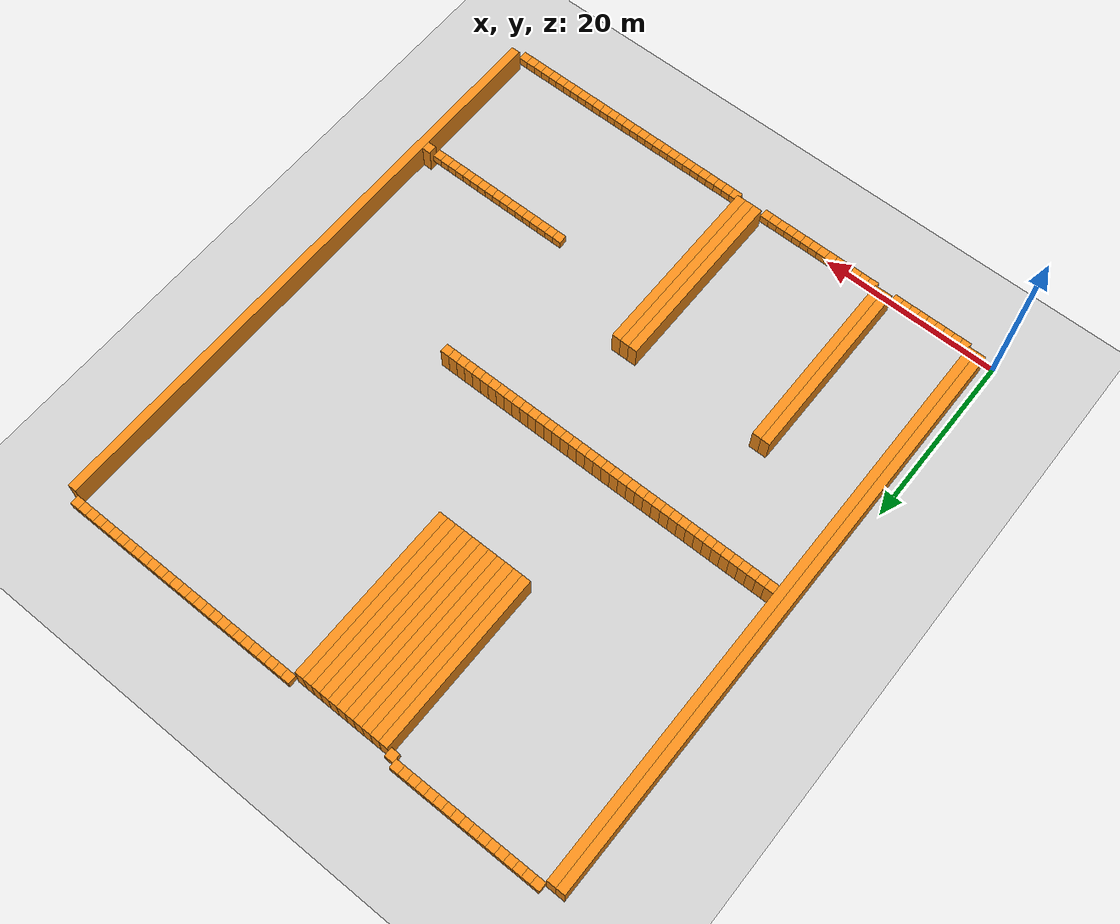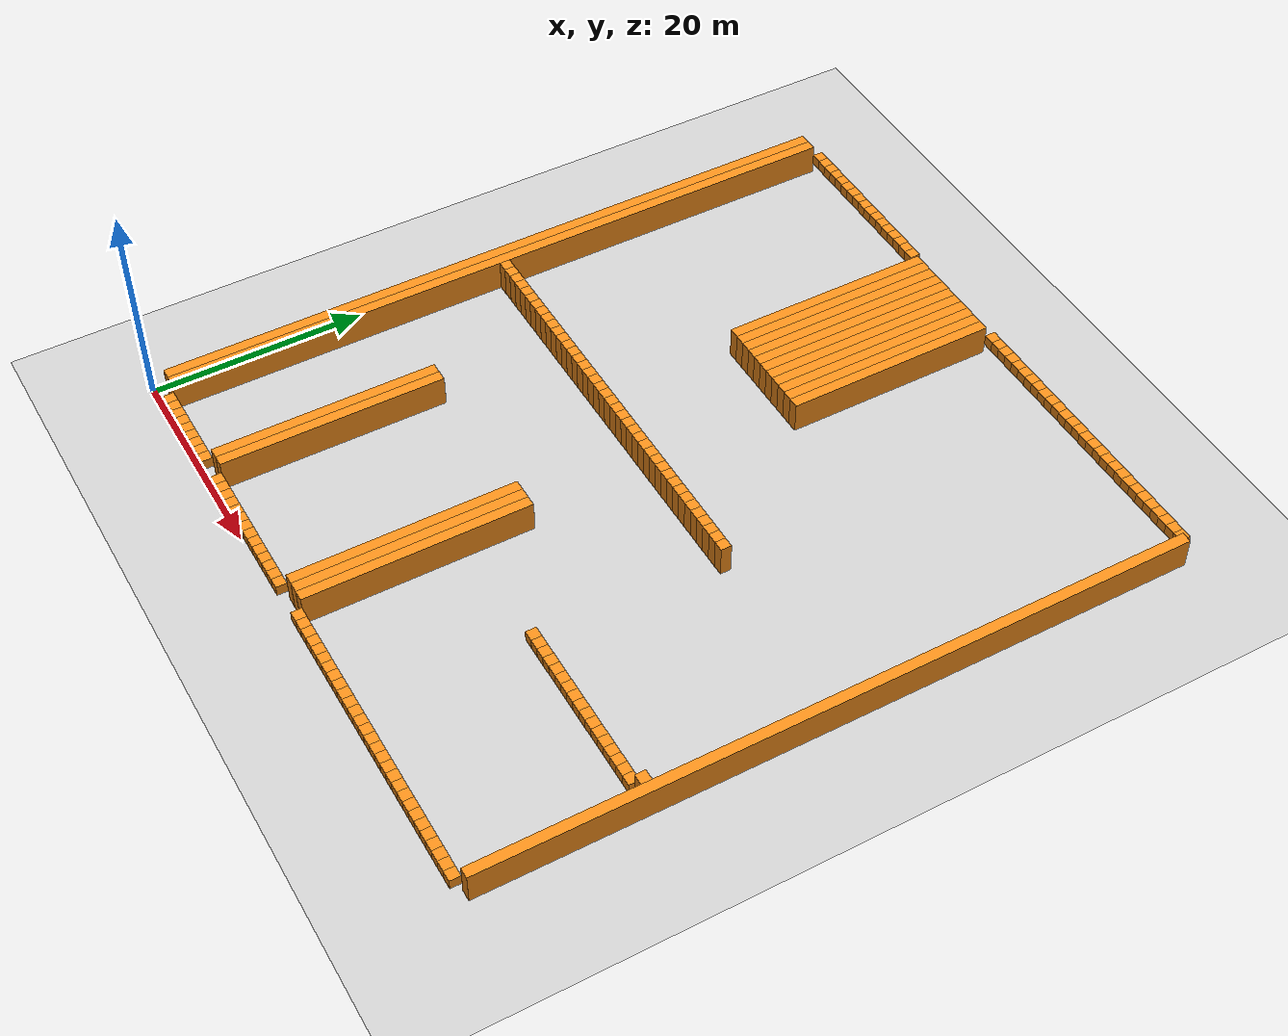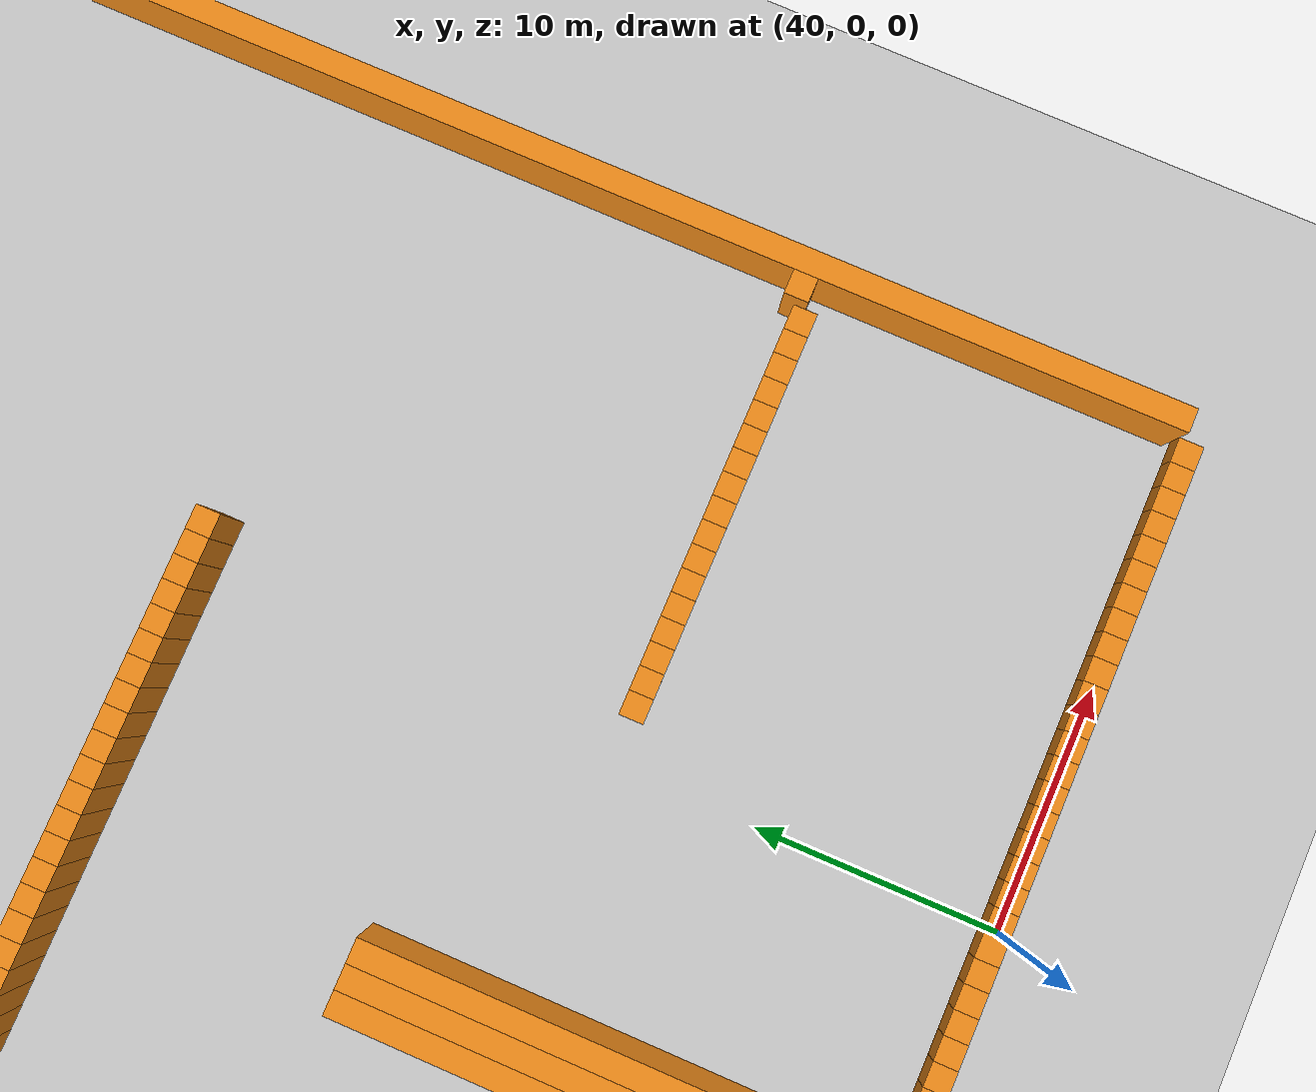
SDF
<sdf version="1.6">
 <world name="default">
  <include><uri>model://ground_plane</uri></include>
  <collision name="collision"><max_contacts>0</max_contacts></collision>
  <light name="sun" type="directional">
   <cast_shadows>0</cast_shadows>
   <pose>0 0 10 0 -0 0</pose>
   <diffuse>0.8 0.8 0.8 1</diffuse>
   <specular>0.2 0.2 0.2 1</specular>
   <attenuation>
    <range>1000</range>
    <constant>0.9</constant>
    <linear>0.01</linear>
    <quadratic>0.001</quadratic>
   </attenuation>
   <direction>-0.5 0.1 -0.9</direction>
  </light>
  <physics name="default_physics" default="0" type="ode"><max_step_size>0.002</max_step_size></physics>
  <gravity>0 0 -9.8</gravity>
  <model name="unit_box_000">
   <pose>1.50    34.00     1.50 0 0 0</pose>
   <static>1</static>
   <link name="link">
    <inertial>
     <mass>5000</mass>
     <inertia><ixx>200</ixx><ixy>0</ixy><ixz>0</ixz><iyy>200</iyy><iyz>0</iyz><izz>200</izz></inertia>
    </inertial>
    <collision name="collision"><geometry><box><size>1 66 3</size></box></geometry></collision>
    <visual name="visual">
     <geometry><box><size>1 66 3</size></box></geometry>
     <material>
      <script><name>Gazebo/Orange</name><uri>file://media/materials/scripts/gazebo.material</uri></script>
     </material>
    </visual>
   </link>
  </model>
  <model name="unit_box_001">
   <pose>2.50    34.00     1.50 0 0 0</pose>
   <static>1</static>
   <link name="link">
    <inertial>
     <mass>5000</mass>
     <inertia><ixx>200</ixx><ixy>0</ixy><ixz>0</ixz><iyy>200</iyy><iyz>0</iyz><izz>200</izz></inertia>
    </inertial>
    <collision name="collision"><geometry><box><size>1 66 3</size></box></geometry></collision>
    <visual name="visual">
     <geometry><box><size>1 66 3</size></box></geometry>
     <material>
      <script><name>Gazebo/Orange</name><uri>file://media/materials/scripts/gazebo.material</uri></script>
     </material>
    </visual>
   </link>
  </model>
  <model name="unit_box_002">
   <pose>3.50     0.50     1.50 0 0 0</pose>
   <static>1</static>
   <link name="link">
    <inertial>
     <mass>5000</mass>
     <inertia><ixx>200</ixx><ixy>0</ixy><ixz>0</ixz><iyy>200</iyy><iyz>0</iyz><izz>200</izz></inertia>
    </inertial>
    <collision name="collision"><geometry><box><size>1 1 1</size></box></geometry></collision>
    <visual name="visual">
     <geometry><box><size>1 1 1</size></box></geometry>
     <material>
      <script><name>Gazebo/Orange</name><uri>file://media/materials/scripts/gazebo.material</uri></script>
     </material>
    </visual>
   </link>
  </model>
  <model name="unit_box_003">
   <pose>3.50    33.50     1.50 0 0 0</pose>
   <static>1</static>
   <link name="link">
    <inertial>
     <mass>5000</mass>
     <inertia><ixx>200</ixx><ixy>0</ixy><ixz>0</ixz><iyy>200</iyy><iyz>0</iyz><izz>200</izz></inertia>
    </inertial>
    <collision name="collision"><geometry><box><size>1 1 3</size></box></geometry></collision>
    <visual name="visual">
     <geometry><box><size>1 1 3</size></box></geometry>
     <material>
      <script><name>Gazebo/Orange</name><uri>file://media/materials/scripts/gazebo.material</uri></script>
     </material>
    </visual>
   </link>
  </model>
  <model name="unit_box_004">
   <pose>3.50    67.50     1.50 0 0 0</pose>
   <static>1</static>
   <link name="link">
    <inertial>
     <mass>5000</mass>
     <inertia><ixx>200</ixx><ixy>0</ixy><ixz>0</ixz><iyy>200</iyy><iyz>0</iyz><izz>200</izz></inertia>
    </inertial>
    <collision name="collision"><geometry><box><size>1 1 1</size></box></geometry></collision>
    <visual name="visual">
     <geometry><box><size>1 1 1</size></box></geometry>
     <material>
      <script><name>Gazebo/Orange</name><uri>file://media/materials/scripts/gazebo.material</uri></script>
     </material>
    </visual>
   </link>
  </model>
  <model name="unit_box_005">
   <pose>4.50     0.50     1.50 0 0 0</pose>
   <static>1</static>
   <link name="link">
    <inertial>
     <mass>5000</mass>
     <inertia><ixx>200</ixx><ixy>0</ixy><ixz>0</ixz><iyy>200</iyy><iyz>0</iyz><izz>200</izz></inertia>
    </inertial>
    <collision name="collision"><geometry><box><size>1 1 1</size></box></geometry></collision>
    <visual name="visual">
     <geometry><box><size>1 1 1</size></box></geometry>
     <material>
      <script><name>Gazebo/Orange</name><uri>file://media/materials/scripts/gazebo.material</uri></script>
     </material>
    </visual>
   </link>
  </model>
  <model name="unit_box_006">
   <pose>4.50    33.50     1.50 0 0 0</pose>
   <static>1</static>
   <link name="link">
    <inertial>
     <mass>5000</mass>
     <inertia><ixx>200</ixx><ixy>0</ixy><ixz>0</ixz><iyy>200</iyy><iyz>0</iyz><izz>200</izz></inertia>
    </inertial>
    <collision name="collision"><geometry><box><size>1 1 3</size></box></geometry></collision>
    <visual name="visual">
     <geometry><box><size>1 1 3</size></box></geometry>
     <material>
      <script><name>Gazebo/Orange</name><uri>file://media/materials/scripts/gazebo.material</uri></script>
     </material>
    </visual>
   </link>
  </model>
  <model name="unit_box_007">
   <pose>4.50    67.50     1.50 0 0 0</pose>
   <static>1</static>
   <link name="link">
    <inertial>
     <mass>5000</mass>
     <inertia><ixx>200</ixx><ixy>0</ixy><ixz>0</ixz><iyy>200</iyy><iyz>0</iyz><izz>200</izz></inertia>
    </inertial>
    <collision name="collision"><geometry><box><size>1 1 1</size></box></geometry></collision>
    <visual name="visual">
     <geometry><box><size>1 1 1</size></box></geometry>
     <material>
      <script><name>Gazebo/Orange</name><uri>file://media/materials/scripts/gazebo.material</uri></script>
     </material>
    </visual>
   </link>
  </model>
  <model name="unit_box_008">
   <pose>5.50     0.50     1.50 0 0 0</pose>
   <static>1</static>
   <link name="link">
    <inertial>
     <mass>5000</mass>
     <inertia><ixx>200</ixx><ixy>0</ixy><ixz>0</ixz><iyy>200</iyy><iyz>0</iyz><izz>200</izz></inertia>
    </inertial>
    <collision name="collision"><geometry><box><size>1 1 1</size></box></geometry></collision>
    <visual name="visual">
     <geometry><box><size>1 1 1</size></box></geometry>
     <material>
      <script><name>Gazebo/Orange</name><uri>file://media/materials/scripts/gazebo.material</uri></script>
     </material>
    </visual>
   </link>
  </model>
  <model name="unit_box_009">
   <pose>5.50    33.50     1.50 0 0 0</pose>
   <static>1</static>
   <link name="link">
    <inertial>
     <mass>5000</mass>
     <inertia><ixx>200</ixx><ixy>0</ixy><ixz>0</ixz><iyy>200</iyy><iyz>0</iyz><izz>200</izz></inertia>
    </inertial>
    <collision name="collision"><geometry><box><size>1 1 3</size></box></geometry></collision>
    <visual name="visual">
     <geometry><box><size>1 1 3</size></box></geometry>
     <material>
      <script><name>Gazebo/Orange</name><uri>file://media/materials/scripts/gazebo.material</uri></script>
     </material>
    </visual>
   </link>
  </model>
  <model name="unit_box_010">
   <pose>5.50    67.50     1.50 0 0 0</pose>
   <static>1</static>
   <link name="link">
    <inertial>
     <mass>5000</mass>
     <inertia><ixx>200</ixx><ixy>0</ixy><ixz>0</ixz><iyy>200</iyy><iyz>0</iyz><izz>200</izz></inertia>
    </inertial>
    <collision name="collision"><geometry><box><size>1 1 1</size></box></geometry></collision>
    <visual name="visual">
     <geometry><box><size>1 1 1</size></box></geometry>
     <material>
      <script><name>Gazebo/Orange</name><uri>file://media/materials/scripts/gazebo.material</uri></script>
     </material>
    </visual>
   </link>
  </model>
  <model name="unit_box_011">
   <pose>6.50     0.50     1.50 0 0 0</pose>
   <static>1</static>
   <link name="link">
    <inertial>
     <mass>5000</mass>
     <inertia><ixx>200</ixx><ixy>0</ixy><ixz>0</ixz><iyy>200</iyy><iyz>0</iyz><izz>200</izz></inertia>
    </inertial>
    <collision name="collision"><geometry><box><size>1 1 1</size></box></geometry></collision>
    <visual name="visual">
     <geometry><box><size>1 1 1</size></box></geometry>
     <material>
      <script><name>Gazebo/Orange</name><uri>file://media/materials/scripts/gazebo.material</uri></script>
     </material>
    </visual>
   </link>
  </model>
  <model name="unit_box_012">
   <pose>6.50    33.50     1.50 0 0 0</pose>
   <static>1</static>
   <link name="link">
    <inertial>
     <mass>5000</mass>
     <inertia><ixx>200</ixx><ixy>0</ixy><ixz>0</ixz><iyy>200</iyy><iyz>0</iyz><izz>200</izz></inertia>
    </inertial>
    <collision name="collision"><geometry><box><size>1 1 3</size></box></geometry></collision>
    <visual name="visual">
     <geometry><box><size>1 1 3</size></box></geometry>
     <material>
      <script><name>Gazebo/Orange</name><uri>file://media/materials/scripts/gazebo.material</uri></script>
     </material>
    </visual>
   </link>
  </model>
  <model name="unit_box_013">
   <pose>6.50    67.50     1.50 0 0 0</pose>
   <static>1</static>
   <link name="link">
    <inertial>
     <mass>5000</mass>
     <inertia><ixx>200</ixx><ixy>0</ixy><ixz>0</ixz><iyy>200</iyy><iyz>0</iyz><izz>200</izz></inertia>
    </inertial>
    <collision name="collision"><geometry><box><size>1 1 1</size></box></geometry></collision>
    <visual name="visual">
     <geometry><box><size>1 1 1</size></box></geometry>
     <material>
      <script><name>Gazebo/Orange</name><uri>file://media/materials/scripts/gazebo.material</uri></script>
     </material>
    </visual>
   </link>
  </model>
  <model name="unit_box_014">
   <pose>7.50     0.50     1.50 0 0 0</pose>
   <static>1</static>
   <link name="link">
    <inertial>
     <mass>5000</mass>
     <inertia><ixx>200</ixx><ixy>0</ixy><ixz>0</ixz><iyy>200</iyy><iyz>0</iyz><izz>200</izz></inertia>
    </inertial>
    <collision name="collision"><geometry><box><size>1 1 1</size></box></geometry></collision>
    <visual name="visual">
     <geometry><box><size>1 1 1</size></box></geometry>
     <material>
      <script><name>Gazebo/Orange</name><uri>file://media/materials/scripts/gazebo.material</uri></script>
     </material>
    </visual>
   </link>
  </model>
  <model name="unit_box_015">
   <pose>7.50    33.50     1.50 0 0 0</pose>
   <static>1</static>
   <link name="link">
    <inertial>
     <mass>5000</mass>
     <inertia><ixx>200</ixx><ixy>0</ixy><ixz>0</ixz><iyy>200</iyy><iyz>0</iyz><izz>200</izz></inertia>
    </inertial>
    <collision name="collision"><geometry><box><size>1 1 3</size></box></geometry></collision>
    <visual name="visual">
     <geometry><box><size>1 1 3</size></box></geometry>
     <material>
      <script><name>Gazebo/Orange</name><uri>file://media/materials/scripts/gazebo.material</uri></script>
     </material>
    </visual>
   </link>
  </model>
  <model name="unit_box_016">
   <pose>7.50    67.50     1.50 0 0 0</pose>
   <static>1</static>
   <link name="link">
    <inertial>
     <mass>5000</mass>
     <inertia><ixx>200</ixx><ixy>0</ixy><ixz>0</ixz><iyy>200</iyy><iyz>0</iyz><izz>200</izz></inertia>
    </inertial>
    <collision name="collision"><geometry><box><size>1 1 1</size></box></geometry></collision>
    <visual name="visual">
     <geometry><box><size>1 1 1</size></box></geometry>
     <material>
      <script><name>Gazebo/Orange</name><uri>file://media/materials/scripts/gazebo.material</uri></script>
     </material>
    </visual>
   </link>
  </model>
  <model name="unit_box_017">
   <pose>8.50     0.50     1.50 0 0 0</pose>
   <static>1</static>
   <link name="link">
    <inertial>
     <mass>5000</mass>
     <inertia><ixx>200</ixx><ixy>0</ixy><ixz>0</ixz><iyy>200</iyy><iyz>0</iyz><izz>200</izz></inertia>
    </inertial>
    <collision name="collision"><geometry><box><size>1 1 1</size></box></geometry></collision>
    <visual name="visual">
     <geometry><box><size>1 1 1</size></box></geometry>
     <material>
      <script><name>Gazebo/Orange</name><uri>file://media/materials/scripts/gazebo.material</uri></script>
     </material>
    </visual>
   </link>
  </model>
  <model name="unit_box_018">
   <pose>8.50    33.50     1.50 0 0 0</pose>
   <static>1</static>
   <link name="link">
    <inertial>
     <mass>5000</mass>
     <inertia><ixx>200</ixx><ixy>0</ixy><ixz>0</ixz><iyy>200</iyy><iyz>0</iyz><izz>200</izz></inertia>
    </inertial>
    <collision name="collision"><geometry><box><size>1 1 3</size></box></geometry></collision>
    <visual name="visual">
     <geometry><box><size>1 1 3</size></box></geometry>
     <material>
      <script><name>Gazebo/Orange</name><uri>file://media/materials/scripts/gazebo.material</uri></script>
     </material>
    </visual>
   </link>
  </model>
  <model name="unit_box_019">
   <pose>8.50    67.50     1.50 0 0 0</pose>
   <static>1</static>
   <link name="link">
    <inertial>
     <mass>5000</mass>
     <inertia><ixx>200</ixx><ixy>0</ixy><ixz>0</ixz><iyy>200</iyy><iyz>0</iyz><izz>200</izz></inertia>
    </inertial>
    <collision name="collision"><geometry><box><size>1 1 1</size></box></geometry></collision>
    <visual name="visual">
     <geometry><box><size>1 1 1</size></box></geometry>
     <material>
      <script><name>Gazebo/Orange</name><uri>file://media/materials/scripts/gazebo.material</uri></script>
     </material>
    </visual>
   </link>
  </model>
  <model name="unit_box_020">
   <pose>9.50     0.50     1.50 0 0 0</pose>
   <static>1</static>
   <link name="link">
    <inertial>
     <mass>5000</mass>
     <inertia><ixx>200</ixx><ixy>0</ixy><ixz>0</ixz><iyy>200</iyy><iyz>0</iyz><izz>200</izz></inertia>
    </inertial>
    <collision name="collision"><geometry><box><size>1 1 1</size></box></geometry></collision>
    <visual name="visual">
     <geometry><box><size>1 1 1</size></box></geometry>
     <material>
      <script><name>Gazebo/Orange</name><uri>file://media/materials/scripts/gazebo.material</uri></script>
     </material>
    </visual>
   </link>
  </model>
  <model name="unit_box_021">
   <pose>9.50    33.50     1.50 0 0 0</pose>
   <static>1</static>
   <link name="link">
    <inertial>
     <mass>5000</mass>
     <inertia><ixx>200</ixx><ixy>0</ixy><ixz>0</ixz><iyy>200</iyy><iyz>0</iyz><izz>200</izz></inertia>
    </inertial>
    <collision name="collision"><geometry><box><size>1 1 3</size></box></geometry></collision>
    <visual name="visual">
     <geometry><box><size>1 1 3</size></box></geometry>
     <material>
      <script><name>Gazebo/Orange</name><uri>file://media/materials/scripts/gazebo.material</uri></script>
     </material>
    </visual>
   </link>
  </model>
  <model name="unit_box_022">
   <pose>9.50    67.50     1.50 0 0 0</pose>
   <static>1</static>
   <link name="link">
    <inertial>
     <mass>5000</mass>
     <inertia><ixx>200</ixx><ixy>0</ixy><ixz>0</ixz><iyy>200</iyy><iyz>0</iyz><izz>200</izz></inertia>
    </inertial>
    <collision name="collision"><geometry><box><size>1 1 1</size></box></geometry></collision>
    <visual name="visual">
     <geometry><box><size>1 1 1</size></box></geometry>
     <material>
      <script><name>Gazebo/Orange</name><uri>file://media/materials/scripts/gazebo.material</uri></script>
     </material>
    </visual>
   </link>
  </model>
  <model name="unit_box_023">
   <pose>10.50     0.50     1.50 0 0 0</pose>
   <static>1</static>
   <link name="link">
    <inertial>
     <mass>5000</mass>
     <inertia><ixx>200</ixx><ixy>0</ixy><ixz>0</ixz><iyy>200</iyy><iyz>0</iyz><izz>200</izz></inertia>
    </inertial>
    <collision name="collision"><geometry><box><size>1 1 1</size></box></geometry></collision>
    <visual name="visual">
     <geometry><box><size>1 1 1</size></box></geometry>
     <material>
      <script><name>Gazebo/Orange</name><uri>file://media/materials/scripts/gazebo.material</uri></script>
     </material>
    </visual>
   </link>
  </model>
  <model name="unit_box_024">
   <pose>10.50    33.50     1.50 0 0 0</pose>
   <static>1</static>
   <link name="link">
    <inertial>
     <mass>5000</mass>
     <inertia><ixx>200</ixx><ixy>0</ixy><ixz>0</ixz><iyy>200</iyy><iyz>0</iyz><izz>200</izz></inertia>
    </inertial>
    <collision name="collision"><geometry><box><size>1 1 3</size></box></geometry></collision>
    <visual name="visual">
     <geometry><box><size>1 1 3</size></box></geometry>
     <material>
      <script><name>Gazebo/Orange</name><uri>file://media/materials/scripts/gazebo.material</uri></script>
     </material>
    </visual>
   </link>
  </model>
  <model name="unit_box_025">
   <pose>10.50    67.50     1.50 0 0 0</pose>
   <static>1</static>
   <link name="link">
    <inertial>
     <mass>5000</mass>
     <inertia><ixx>200</ixx><ixy>0</ixy><ixz>0</ixz><iyy>200</iyy><iyz>0</iyz><izz>200</izz></inertia>
    </inertial>
    <collision name="collision"><geometry><box><size>1 1 1</size></box></geometry></collision>
    <visual name="visual">
     <geometry><box><size>1 1 1</size></box></geometry>
     <material>
      <script><name>Gazebo/Orange</name><uri>file://media/materials/scripts/gazebo.material</uri></script>
     </material>
    </visual>
   </link>
  </model>
  <model name="unit_box_026">
   <pose>11.50     0.50     1.50 0 0 0</pose>
   <static>1</static>
   <link name="link">
    <inertial>
     <mass>5000</mass>
     <inertia><ixx>200</ixx><ixy>0</ixy><ixz>0</ixz><iyy>200</iyy><iyz>0</iyz><izz>200</izz></inertia>
    </inertial>
    <collision name="collision"><geometry><box><size>1 1 1</size></box></geometry></collision>
    <visual name="visual">
     <geometry><box><size>1 1 1</size></box></geometry>
     <material>
      <script><name>Gazebo/Orange</name><uri>file://media/materials/scripts/gazebo.material</uri></script>
     </material>
    </visual>
   </link>
  </model>
  <model name="unit_box_027">
   <pose>11.50    33.50     1.50 0 0 0</pose>
   <static>1</static>
   <link name="link">
    <inertial>
     <mass>5000</mass>
     <inertia><ixx>200</ixx><ixy>0</ixy><ixz>0</ixz><iyy>200</iyy><iyz>0</iyz><izz>200</izz></inertia>
    </inertial>
    <collision name="collision"><geometry><box><size>1 1 3</size></box></geometry></collision>
    <visual name="visual">
     <geometry><box><size>1 1 3</size></box></geometry>
     <material>
      <script><name>Gazebo/Orange</name><uri>file://media/materials/scripts/gazebo.material</uri></script>
     </material>
    </visual>
   </link>
  </model>
  <model name="unit_box_028">
   <pose>11.50    67.50     1.50 0 0 0</pose>
   <static>1</static>
   <link name="link">
    <inertial>
     <mass>5000</mass>
     <inertia><ixx>200</ixx><ixy>0</ixy><ixz>0</ixz><iyy>200</iyy><iyz>0</iyz><izz>200</izz></inertia>
    </inertial>
    <collision name="collision"><geometry><box><size>1 1 1</size></box></geometry></collision>
    <visual name="visual">
     <geometry><box><size>1 1 1</size></box></geometry>
     <material>
      <script><name>Gazebo/Orange</name><uri>file://media/materials/scripts/gazebo.material</uri></script>
     </material>
    </visual>
   </link>
  </model>
  <model name="unit_box_029">
   <pose>12.50    11.50     1.50 0 0 0</pose>
   <static>1</static>
   <link name="link">
    <inertial>
     <mass>5000</mass>
     <inertia><ixx>200</ixx><ixy>0</ixy><ixz>0</ixz><iyy>200</iyy><iyz>0</iyz><izz>200</izz></inertia>
    </inertial>
    <collision name="collision"><geometry><box><size>1 21 3</size></box></geometry></collision>
    <visual name="visual">
     <geometry><box><size>1 21 3</size></box></geometry>
     <material>
      <script><name>Gazebo/Orange</name><uri>file://media/materials/scripts/gazebo.material</uri></script>
     </material>
    </visual>
   </link>
  </model>
  <model name="unit_box_030">
   <pose>12.50    33.50     1.50 0 0 0</pose>
   <static>1</static>
   <link name="link">
    <inertial>
     <mass>5000</mass>
     <inertia><ixx>200</ixx><ixy>0</ixy><ixz>0</ixz><iyy>200</iyy><iyz>0</iyz><izz>200</izz></inertia>
    </inertial>
    <collision name="collision"><geometry><box><size>1 1 3</size></box></geometry></collision>
    <visual name="visual">
     <geometry><box><size>1 1 3</size></box></geometry>
     <material>
      <script><name>Gazebo/Orange</name><uri>file://media/materials/scripts/gazebo.material</uri></script>
     </material>
    </visual>
   </link>
  </model>
  <model name="unit_box_031">
   <pose>12.50    67.50     1.50 0 0 0</pose>
   <static>1</static>
   <link name="link">
    <inertial>
     <mass>5000</mass>
     <inertia><ixx>200</ixx><ixy>0</ixy><ixz>0</ixz><iyy>200</iyy><iyz>0</iyz><izz>200</izz></inertia>
    </inertial>
    <collision name="collision"><geometry><box><size>1 1 1</size></box></geometry></collision>
    <visual name="visual">
     <geometry><box><size>1 1 1</size></box></geometry>
     <material>
      <script><name>Gazebo/Orange</name><uri>file://media/materials/scripts/gazebo.material</uri></script>
     </material>
    </visual>
   </link>
  </model>
  <model name="unit_box_032">
   <pose>13.50    11.50     1.50 0 0 0</pose>
   <static>1</static>
   <link name="link">
    <inertial>
     <mass>5000</mass>
     <inertia><ixx>200</ixx><ixy>0</ixy><ixz>0</ixz><iyy>200</iyy><iyz>0</iyz><izz>200</izz></inertia>
    </inertial>
    <collision name="collision"><geometry><box><size>1 21 3</size></box></geometry></collision>
    <visual name="visual">
     <geometry><box><size>1 21 3</size></box></geometry>
     <material>
      <script><name>Gazebo/Orange</name><uri>file://media/materials/scripts/gazebo.material</uri></script>
     </material>
    </visual>
   </link>
  </model>
  <model name="unit_box_033">
   <pose>13.50    33.50     1.50 0 0 0</pose>
   <static>1</static>
   <link name="link">
    <inertial>
     <mass>5000</mass>
     <inertia><ixx>200</ixx><ixy>0</ixy><ixz>0</ixz><iyy>200</iyy><iyz>0</iyz><izz>200</izz></inertia>
    </inertial>
    <collision name="collision"><geometry><box><size>1 1 3</size></box></geometry></collision>
    <visual name="visual">
     <geometry><box><size>1 1 3</size></box></geometry>
     <material>
      <script><name>Gazebo/Orange</name><uri>file://media/materials/scripts/gazebo.material</uri></script>
     </material>
    </visual>
   </link>
  </model>
  <model name="unit_box_034">
   <pose>13.50    67.50     1.50 0 0 0</pose>
   <static>1</static>
   <link name="link">
    <inertial>
     <mass>5000</mass>
     <inertia><ixx>200</ixx><ixy>0</ixy><ixz>0</ixz><iyy>200</iyy><iyz>0</iyz><izz>200</izz></inertia>
    </inertial>
    <collision name="collision"><geometry><box><size>1 1 1</size></box></geometry></collision>
    <visual name="visual">
     <geometry><box><size>1 1 1</size></box></geometry>
     <material>
      <script><name>Gazebo/Orange</name><uri>file://media/materials/scripts/gazebo.material</uri></script>
     </material>
    </visual>
   </link>
  </model>
  <model name="unit_box_035">
   <pose>14.50     0.50     1.50 0 0 0</pose>
   <static>1</static>
   <link name="link">
    <inertial>
     <mass>5000</mass>
     <inertia><ixx>200</ixx><ixy>0</ixy><ixz>0</ixz><iyy>200</iyy><iyz>0</iyz><izz>200</izz></inertia>
    </inertial>
    <collision name="collision"><geometry><box><size>1 1 1</size></box></geometry></collision>
    <visual name="visual">
     <geometry><box><size>1 1 1</size></box></geometry>
     <material>
      <script><name>Gazebo/Orange</name><uri>file://media/materials/scripts/gazebo.material</uri></script>
     </material>
    </visual>
   </link>
  </model>
  <model name="unit_box_036">
   <pose>14.50    33.50     1.50 0 0 0</pose>
   <static>1</static>
   <link name="link">
    <inertial>
     <mass>5000</mass>
     <inertia><ixx>200</ixx><ixy>0</ixy><ixz>0</ixz><iyy>200</iyy><iyz>0</iyz><izz>200</izz></inertia>
    </inertial>
    <collision name="collision"><geometry><box><size>1 1 3</size></box></geometry></collision>
    <visual name="visual">
     <geometry><box><size>1 1 3</size></box></geometry>
     <material>
      <script><name>Gazebo/Orange</name><uri>file://media/materials/scripts/gazebo.material</uri></script>
     </material>
    </visual>
   </link>
  </model>
  <model name="unit_box_037">
   <pose>14.50    67.50     1.50 0 0 0</pose>
   <static>1</static>
   <link name="link">
    <inertial>
     <mass>5000</mass>
     <inertia><ixx>200</ixx><ixy>0</ixy><ixz>0</ixz><iyy>200</iyy><iyz>0</iyz><izz>200</izz></inertia>
    </inertial>
    <collision name="collision"><geometry><box><size>1 1 1</size></box></geometry></collision>
    <visual name="visual">
     <geometry><box><size>1 1 1</size></box></geometry>
     <material>
      <script><name>Gazebo/Orange</name><uri>file://media/materials/scripts/gazebo.material</uri></script>
     </material>
    </visual>
   </link>
  </model>
  <model name="unit_box_038">
   <pose>15.50     0.50     1.50 0 0 0</pose>
   <static>1</static>
   <link name="link">
    <inertial>
     <mass>5000</mass>
     <inertia><ixx>200</ixx><ixy>0</ixy><ixz>0</ixz><iyy>200</iyy><iyz>0</iyz><izz>200</izz></inertia>
    </inertial>
    <collision name="collision"><geometry><box><size>1 1 1</size></box></geometry></collision>
    <visual name="visual">
     <geometry><box><size>1 1 1</size></box></geometry>
     <material>
      <script><name>Gazebo/Orange</name><uri>file://media/materials/scripts/gazebo.material</uri></script>
     </material>
    </visual>
   </link>
  </model>
  <model name="unit_box_039">
   <pose>15.50    33.50     1.50 0 0 0</pose>
   <static>1</static>
   <link name="link">
    <inertial>
     <mass>5000</mass>
     <inertia><ixx>200</ixx><ixy>0</ixy><ixz>0</ixz><iyy>200</iyy><iyz>0</iyz><izz>200</izz></inertia>
    </inertial>
    <collision name="collision"><geometry><box><size>1 1 3</size></box></geometry></collision>
    <visual name="visual">
     <geometry><box><size>1 1 3</size></box></geometry>
     <material>
      <script><name>Gazebo/Orange</name><uri>file://media/materials/scripts/gazebo.material</uri></script>
     </material>
    </visual>
   </link>
  </model>
  <model name="unit_box_040">
   <pose>15.50    67.50     1.50 0 0 0</pose>
   <static>1</static>
   <link name="link">
    <inertial>
     <mass>5000</mass>
     <inertia><ixx>200</ixx><ixy>0</ixy><ixz>0</ixz><iyy>200</iyy><iyz>0</iyz><izz>200</izz></inertia>
    </inertial>
    <collision name="collision"><geometry><box><size>1 1 1</size></box></geometry></collision>
    <visual name="visual">
     <geometry><box><size>1 1 1</size></box></geometry>
     <material>
      <script><name>Gazebo/Orange</name><uri>file://media/materials/scripts/gazebo.material</uri></script>
     </material>
    </visual>
   </link>
  </model>
  <model name="unit_box_041">
   <pose>16.50     0.50     1.50 0 0 0</pose>
   <static>1</static>
   <link name="link">
    <inertial>
     <mass>5000</mass>
     <inertia><ixx>200</ixx><ixy>0</ixy><ixz>0</ixz><iyy>200</iyy><iyz>0</iyz><izz>200</izz></inertia>
    </inertial>
    <collision name="collision"><geometry><box><size>1 1 1</size></box></geometry></collision>
    <visual name="visual">
     <geometry><box><size>1 1 1</size></box></geometry>
     <material>
      <script><name>Gazebo/Orange</name><uri>file://media/materials/scripts/gazebo.material</uri></script>
     </material>
    </visual>
   </link>
  </model>
  <model name="unit_box_042">
   <pose>16.50    33.50     1.50 0 0 0</pose>
   <static>1</static>
   <link name="link">
    <inertial>
     <mass>5000</mass>
     <inertia><ixx>200</ixx><ixy>0</ixy><ixz>0</ixz><iyy>200</iyy><iyz>0</iyz><izz>200</izz></inertia>
    </inertial>
    <collision name="collision"><geometry><box><size>1 1 3</size></box></geometry></collision>
    <visual name="visual">
     <geometry><box><size>1 1 3</size></box></geometry>
     <material>
      <script><name>Gazebo/Orange</name><uri>file://media/materials/scripts/gazebo.material</uri></script>
     </material>
    </visual>
   </link>
  </model>
  <model name="unit_box_043">
   <pose>16.50    67.50     1.50 0 0 0</pose>
   <static>1</static>
   <link name="link">
    <inertial>
     <mass>5000</mass>
     <inertia><ixx>200</ixx><ixy>0</ixy><ixz>0</ixz><iyy>200</iyy><iyz>0</iyz><izz>200</izz></inertia>
    </inertial>
    <collision name="collision"><geometry><box><size>1 1 1</size></box></geometry></collision>
    <visual name="visual">
     <geometry><box><size>1 1 1</size></box></geometry>
     <material>
      <script><name>Gazebo/Orange</name><uri>file://media/materials/scripts/gazebo.material</uri></script>
     </material>
    </visual>
   </link>
  </model>
  <model name="unit_box_044">
   <pose>17.50     0.50     1.50 0 0 0</pose>
   <static>1</static>
   <link name="link">
    <inertial>
     <mass>5000</mass>
     <inertia><ixx>200</ixx><ixy>0</ixy><ixz>0</ixz><iyy>200</iyy><iyz>0</iyz><izz>200</izz></inertia>
    </inertial>
    <collision name="collision"><geometry><box><size>1 1 1</size></box></geometry></collision>
    <visual name="visual">
     <geometry><box><size>1 1 1</size></box></geometry>
     <material>
      <script><name>Gazebo/Orange</name><uri>file://media/materials/scripts/gazebo.material</uri></script>
     </material>
    </visual>
   </link>
  </model>
  <model name="unit_box_045">
   <pose>17.50    33.50     1.50 0 0 0</pose>
   <static>1</static>
   <link name="link">
    <inertial>
     <mass>5000</mass>
     <inertia><ixx>200</ixx><ixy>0</ixy><ixz>0</ixz><iyy>200</iyy><iyz>0</iyz><izz>200</izz></inertia>
    </inertial>
    <collision name="collision"><geometry><box><size>1 1 3</size></box></geometry></collision>
    <visual name="visual">
     <geometry><box><size>1 1 3</size></box></geometry>
     <material>
      <script><name>Gazebo/Orange</name><uri>file://media/materials/scripts/gazebo.material</uri></script>
     </material>
    </visual>
   </link>
  </model>
  <model name="unit_box_046">
   <pose>17.50    67.50     1.50 0 0 0</pose>
   <static>1</static>
   <link name="link">
    <inertial>
     <mass>5000</mass>
     <inertia><ixx>200</ixx><ixy>0</ixy><ixz>0</ixz><iyy>200</iyy><iyz>0</iyz><izz>200</izz></inertia>
    </inertial>
    <collision name="collision"><geometry><box><size>1 1 1</size></box></geometry></collision>
    <visual name="visual">
     <geometry><box><size>1 1 1</size></box></geometry>
     <material>
      <script><name>Gazebo/Orange</name><uri>file://media/materials/scripts/gazebo.material</uri></script>
     </material>
    </visual>
   </link>
  </model>
  <model name="unit_box_047">
   <pose>18.50     0.50     1.50 0 0 0</pose>
   <static>1</static>
   <link name="link">
    <inertial>
     <mass>5000</mass>
     <inertia><ixx>200</ixx><ixy>0</ixy><ixz>0</ixz><iyy>200</iyy><iyz>0</iyz><izz>200</izz></inertia>
    </inertial>
    <collision name="collision"><geometry><box><size>1 1 1</size></box></geometry></collision>
    <visual name="visual">
     <geometry><box><size>1 1 1</size></box></geometry>
     <material>
      <script><name>Gazebo/Orange</name><uri>file://media/materials/scripts/gazebo.material</uri></script>
     </material>
    </visual>
   </link>
  </model>
  <model name="unit_box_048">
   <pose>18.50    33.50     1.50 0 0 0</pose>
   <static>1</static>
   <link name="link">
    <inertial>
     <mass>5000</mass>
     <inertia><ixx>200</ixx><ixy>0</ixy><ixz>0</ixz><iyy>200</iyy><iyz>0</iyz><izz>200</izz></inertia>
    </inertial>
    <collision name="collision"><geometry><box><size>1 1 3</size></box></geometry></collision>
    <visual name="visual">
     <geometry><box><size>1 1 3</size></box></geometry>
     <material>
      <script><name>Gazebo/Orange</name><uri>file://media/materials/scripts/gazebo.material</uri></script>
     </material>
    </visual>
   </link>
  </model>
  <model name="unit_box_049">
   <pose>18.50    67.50     1.50 0 0 0</pose>
   <static>1</static>
   <link name="link">
    <inertial>
     <mass>5000</mass>
     <inertia><ixx>200</ixx><ixy>0</ixy><ixz>0</ixz><iyy>200</iyy><iyz>0</iyz><izz>200</izz></inertia>
    </inertial>
    <collision name="collision"><geometry><box><size>1 1 1</size></box></geometry></collision>
    <visual name="visual">
     <geometry><box><size>1 1 1</size></box></geometry>
     <material>
      <script><name>Gazebo/Orange</name><uri>file://media/materials/scripts/gazebo.material</uri></script>
     </material>
    </visual>
   </link>
  </model>
  <model name="unit_box_050">
   <pose>19.50     0.50     1.50 0 0 0</pose>
   <static>1</static>
   <link name="link">
    <inertial>
     <mass>5000</mass>
     <inertia><ixx>200</ixx><ixy>0</ixy><ixz>0</ixz><iyy>200</iyy><iyz>0</iyz><izz>200</izz></inertia>
    </inertial>
    <collision name="collision"><geometry><box><size>1 1 1</size></box></geometry></collision>
    <visual name="visual">
     <geometry><box><size>1 1 1</size></box></geometry>
     <material>
      <script><name>Gazebo/Orange</name><uri>file://media/materials/scripts/gazebo.material</uri></script>
     </material>
    </visual>
   </link>
  </model>
  <model name="unit_box_051">
   <pose>19.50    33.50     1.50 0 0 0</pose>
   <static>1</static>
   <link name="link">
    <inertial>
     <mass>5000</mass>
     <inertia><ixx>200</ixx><ixy>0</ixy><ixz>0</ixz><iyy>200</iyy><iyz>0</iyz><izz>200</izz></inertia>
    </inertial>
    <collision name="collision"><geometry><box><size>1 1 3</size></box></geometry></collision>
    <visual name="visual">
     <geometry><box><size>1 1 3</size></box></geometry>
     <material>
      <script><name>Gazebo/Orange</name><uri>file://media/materials/scripts/gazebo.material</uri></script>
     </material>
    </visual>
   </link>
  </model>
  <model name="unit_box_052">
   <pose>19.50    67.50     1.50 0 0 0</pose>
   <static>1</static>
   <link name="link">
    <inertial>
     <mass>5000</mass>
     <inertia><ixx>200</ixx><ixy>0</ixy><ixz>0</ixz><iyy>200</iyy><iyz>0</iyz><izz>200</izz></inertia>
    </inertial>
    <collision name="collision"><geometry><box><size>1 1 1</size></box></geometry></collision>
    <visual name="visual">
     <geometry><box><size>1 1 1</size></box></geometry>
     <material>
      <script><name>Gazebo/Orange</name><uri>file://media/materials/scripts/gazebo.material</uri></script>
     </material>
    </visual>
   </link>
  </model>
  <model name="unit_box_053">
   <pose>20.50     0.50     1.50 0 0 0</pose>
   <static>1</static>
   <link name="link">
    <inertial>
     <mass>5000</mass>
     <inertia><ixx>200</ixx><ixy>0</ixy><ixz>0</ixz><iyy>200</iyy><iyz>0</iyz><izz>200</izz></inertia>
    </inertial>
    <collision name="collision"><geometry><box><size>1 1 1</size></box></geometry></collision>
    <visual name="visual">
     <geometry><box><size>1 1 1</size></box></geometry>
     <material>
      <script><name>Gazebo/Orange</name><uri>file://media/materials/scripts/gazebo.material</uri></script>
     </material>
    </visual>
   </link>
  </model>
  <model name="unit_box_054">
   <pose>20.50    33.50     1.50 0 0 0</pose>
   <static>1</static>
   <link name="link">
    <inertial>
     <mass>5000</mass>
     <inertia><ixx>200</ixx><ixy>0</ixy><ixz>0</ixz><iyy>200</iyy><iyz>0</iyz><izz>200</izz></inertia>
    </inertial>
    <collision name="collision"><geometry><box><size>1 1 3</size></box></geometry></collision>
    <visual name="visual">
     <geometry><box><size>1 1 3</size></box></geometry>
     <material>
      <script><name>Gazebo/Orange</name><uri>file://media/materials/scripts/gazebo.material</uri></script>
     </material>
    </visual>
   </link>
  </model>
  <model name="unit_box_055">
   <pose>20.50    67.00     1.50 0 0 0</pose>
   <static>1</static>
   <link name="link">
    <inertial>
     <mass>5000</mass>
     <inertia><ixx>200</ixx><ixy>0</ixy><ixz>0</ixz><iyy>200</iyy><iyz>0</iyz><izz>200</izz></inertia>
    </inertial>
    <collision name="collision"><geometry><box><size>1 1 1</size></box></geometry></collision>
    <visual name="visual">
     <geometry><box><size>1 1 1</size></box></geometry>
     <material>
      <script><name>Gazebo/Orange</name><uri>file://media/materials/scripts/gazebo.material</uri></script>
     </material>
    </visual>
   </link>
  </model>
  <model name="unit_box_056">
   <pose>21.50     0.50     1.50 0 0 0</pose>
   <static>1</static>
   <link name="link">
    <inertial>
     <mass>5000</mass>
     <inertia><ixx>200</ixx><ixy>0</ixy><ixz>0</ixz><iyy>200</iyy><iyz>0</iyz><izz>200</izz></inertia>
    </inertial>
    <collision name="collision"><geometry><box><size>1 1 1</size></box></geometry></collision>
    <visual name="visual">
     <geometry><box><size>1 1 1</size></box></geometry>
     <material>
      <script><name>Gazebo/Orange</name><uri>file://media/materials/scripts/gazebo.material</uri></script>
     </material>
    </visual>
   </link>
  </model>
  <model name="unit_box_057">
   <pose>21.50    33.50     1.50 0 0 0</pose>
   <static>1</static>
   <link name="link">
    <inertial>
     <mass>5000</mass>
     <inertia><ixx>200</ixx><ixy>0</ixy><ixz>0</ixz><iyy>200</iyy><iyz>0</iyz><izz>200</izz></inertia>
    </inertial>
    <collision name="collision"><geometry><box><size>1 1 3</size></box></geometry></collision>
    <visual name="visual">
     <geometry><box><size>1 1 3</size></box></geometry>
     <material>
      <script><name>Gazebo/Orange</name><uri>file://media/materials/scripts/gazebo.material</uri></script>
     </material>
    </visual>
   </link>
  </model>
  <model name="unit_box_058">
   <pose>21.50    57.00     1.50 0 0 0</pose>
   <static>1</static>
   <link name="link">
    <inertial>
     <mass>5000</mass>
     <inertia><ixx>200</ixx><ixy>0</ixy><ixz>0</ixz><iyy>200</iyy><iyz>0</iyz><izz>200</izz></inertia>
    </inertial>
    <collision name="collision"><geometry><box><size>1 20 3</size></box></geometry></collision>
    <visual name="visual">
     <geometry><box><size>1 20 3</size></box></geometry>
     <material>
      <script><name>Gazebo/Orange</name><uri>file://media/materials/scripts/gazebo.material</uri></script>
     </material>
    </visual>
   </link>
  </model>
  <model name="unit_box_059">
   <pose>22.50     0.50     1.50 0 0 0</pose>
   <static>1</static>
   <link name="link">
    <inertial>
     <mass>5000</mass>
     <inertia><ixx>200</ixx><ixy>0</ixy><ixz>0</ixz><iyy>200</iyy><iyz>0</iyz><izz>200</izz></inertia>
    </inertial>
    <collision name="collision"><geometry><box><size>1 1 1</size></box></geometry></collision>
    <visual name="visual">
     <geometry><box><size>1 1 1</size></box></geometry>
     <material>
      <script><name>Gazebo/Orange</name><uri>file://media/materials/scripts/gazebo.material</uri></script>
     </material>
    </visual>
   </link>
  </model>
  <model name="unit_box_060">
   <pose>22.50    33.50     1.50 0 0 0</pose>
   <static>1</static>
   <link name="link">
    <inertial>
     <mass>5000</mass>
     <inertia><ixx>200</ixx><ixy>0</ixy><ixz>0</ixz><iyy>200</iyy><iyz>0</iyz><izz>200</izz></inertia>
    </inertial>
    <collision name="collision"><geometry><box><size>1 1 3</size></box></geometry></collision>
    <visual name="visual">
     <geometry><box><size>1 1 3</size></box></geometry>
     <material>
      <script><name>Gazebo/Orange</name><uri>file://media/materials/scripts/gazebo.material</uri></script>
     </material>
    </visual>
   </link>
  </model>
  <model name="unit_box_061">
   <pose>22.50    57.00     1.50 0 0 0</pose>
   <static>1</static>
   <link name="link">
    <inertial>
     <mass>5000</mass>
     <inertia><ixx>200</ixx><ixy>0</ixy><ixz>0</ixz><iyy>200</iyy><iyz>0</iyz><izz>200</izz></inertia>
    </inertial>
    <collision name="collision"><geometry><box><size>1 20 3</size></box></geometry></collision>
    <visual name="visual">
     <geometry><box><size>1 20 3</size></box></geometry>
     <material>
      <script><name>Gazebo/Orange</name><uri>file://media/materials/scripts/gazebo.material</uri></script>
     </material>
    </visual>
   </link>
  </model>
  <model name="unit_box_062">
   <pose>23.50     0.50     1.50 0 0 0</pose>
   <static>1</static>
   <link name="link">
    <inertial>
     <mass>5000</mass>
     <inertia><ixx>200</ixx><ixy>0</ixy><ixz>0</ixz><iyy>200</iyy><iyz>0</iyz><izz>200</izz></inertia>
    </inertial>
    <collision name="collision"><geometry><box><size>1 1 1</size></box></geometry></collision>
    <visual name="visual">
     <geometry><box><size>1 1 1</size></box></geometry>
     <material>
      <script><name>Gazebo/Orange</name><uri>file://media/materials/scripts/gazebo.material</uri></script>
     </material>
    </visual>
   </link>
  </model>
  <model name="unit_box_063">
   <pose>23.50    33.50     1.50 0 0 0</pose>
   <static>1</static>
   <link name="link">
    <inertial>
     <mass>5000</mass>
     <inertia><ixx>200</ixx><ixy>0</ixy><ixz>0</ixz><iyy>200</iyy><iyz>0</iyz><izz>200</izz></inertia>
    </inertial>
    <collision name="collision"><geometry><box><size>1 1 3</size></box></geometry></collision>
    <visual name="visual">
     <geometry><box><size>1 1 3</size></box></geometry>
     <material>
      <script><name>Gazebo/Orange</name><uri>file://media/materials/scripts/gazebo.material</uri></script>
     </material>
    </visual>
   </link>
  </model>
  <model name="unit_box_064">
   <pose>23.50    57.00     1.50 0 0 0</pose>
   <static>1</static>
   <link name="link">
    <inertial>
     <mass>5000</mass>
     <inertia><ixx>200</ixx><ixy>0</ixy><ixz>0</ixz><iyy>200</iyy><iyz>0</iyz><izz>200</izz></inertia>
    </inertial>
    <collision name="collision"><geometry><box><size>1 20 3</size></box></geometry></collision>
    <visual name="visual">
     <geometry><box><size>1 20 3</size></box></geometry>
     <material>
      <script><name>Gazebo/Orange</name><uri>file://media/materials/scripts/gazebo.material</uri></script>
     </material>
    </visual>
   </link>
  </model>
  <model name="unit_box_065">
   <pose>24.50     0.50     1.50 0 0 0</pose>
   <static>1</static>
   <link name="link">
    <inertial>
     <mass>5000</mass>
     <inertia><ixx>200</ixx><ixy>0</ixy><ixz>0</ixz><iyy>200</iyy><iyz>0</iyz><izz>200</izz></inertia>
    </inertial>
    <collision name="collision"><geometry><box><size>1 1 1</size></box></geometry></collision>
    <visual name="visual">
     <geometry><box><size>1 1 1</size></box></geometry>
     <material>
      <script><name>Gazebo/Orange</name><uri>file://media/materials/scripts/gazebo.material</uri></script>
     </material>
    </visual>
   </link>
  </model>
  <model name="unit_box_066">
   <pose>24.50    33.50     1.50 0 0 0</pose>
   <static>1</static>
   <link name="link">
    <inertial>
     <mass>5000</mass>
     <inertia><ixx>200</ixx><ixy>0</ixy><ixz>0</ixz><iyy>200</iyy><iyz>0</iyz><izz>200</izz></inertia>
    </inertial>
    <collision name="collision"><geometry><box><size>1 1 3</size></box></geometry></collision>
    <visual name="visual">
     <geometry><box><size>1 1 3</size></box></geometry>
     <material>
      <script><name>Gazebo/Orange</name><uri>file://media/materials/scripts/gazebo.material</uri></script>
     </material>
    </visual>
   </link>
  </model>
  <model name="unit_box_067">
   <pose>24.50    57.00     1.50 0 0 0</pose>
   <static>1</static>
   <link name="link">
    <inertial>
     <mass>5000</mass>
     <inertia><ixx>200</ixx><ixy>0</ixy><ixz>0</ixz><iyy>200</iyy><iyz>0</iyz><izz>200</izz></inertia>
    </inertial>
    <collision name="collision"><geometry><box><size>1 20 3</size></box></geometry></collision>
    <visual name="visual">
     <geometry><box><size>1 20 3</size></box></geometry>
     <material>
      <script><name>Gazebo/Orange</name><uri>file://media/materials/scripts/gazebo.material</uri></script>
     </material>
    </visual>
   </link>
  </model>
  <model name="unit_box_068">
   <pose>25.50     0.50     1.50 0 0 0</pose>
   <static>1</static>
   <link name="link">
    <inertial>
     <mass>5000</mass>
     <inertia><ixx>200</ixx><ixy>0</ixy><ixz>0</ixz><iyy>200</iyy><iyz>0</iyz><izz>200</izz></inertia>
    </inertial>
    <collision name="collision"><geometry><box><size>1 1 1</size></box></geometry></collision>
    <visual name="visual">
     <geometry><box><size>1 1 1</size></box></geometry>
     <material>
      <script><name>Gazebo/Orange</name><uri>file://media/materials/scripts/gazebo.material</uri></script>
     </material>
    </visual>
   </link>
  </model>
  <model name="unit_box_069">
   <pose>25.50    33.50     1.50 0 0 0</pose>
   <static>1</static>
   <link name="link">
    <inertial>
     <mass>5000</mass>
     <inertia><ixx>200</ixx><ixy>0</ixy><ixz>0</ixz><iyy>200</iyy><iyz>0</iyz><izz>200</izz></inertia>
    </inertial>
    <collision name="collision"><geometry><box><size>1 1 3</size></box></geometry></collision>
    <visual name="visual">
     <geometry><box><size>1 1 3</size></box></geometry>
     <material>
      <script><name>Gazebo/Orange</name><uri>file://media/materials/scripts/gazebo.material</uri></script>
     </material>
    </visual>
   </link>
  </model>
  <model name="unit_box_070">
   <pose>25.50    57.00     1.50 0 0 0</pose>
   <static>1</static>
   <link name="link">
    <inertial>
     <mass>5000</mass>
     <inertia><ixx>200</ixx><ixy>0</ixy><ixz>0</ixz><iyy>200</iyy><iyz>0</iyz><izz>200</izz></inertia>
    </inertial>
    <collision name="collision"><geometry><box><size>1 20 3</size></box></geometry></collision>
    <visual name="visual">
     <geometry><box><size>1 20 3</size></box></geometry>
     <material>
      <script><name>Gazebo/Orange</name><uri>file://media/materials/scripts/gazebo.material</uri></script>
     </material>
    </visual>
   </link>
  </model>
  <model name="unit_box_071">
   <pose>26.50     0.50     1.50 0 0 0</pose>
   <static>1</static>
   <link name="link">
    <inertial>
     <mass>5000</mass>
     <inertia><ixx>200</ixx><ixy>0</ixy><ixz>0</ixz><iyy>200</iyy><iyz>0</iyz><izz>200</izz></inertia>
    </inertial>
    <collision name="collision"><geometry><box><size>1 1 1</size></box></geometry></collision>
    <visual name="visual">
     <geometry><box><size>1 1 1</size></box></geometry>
     <material>
      <script><name>Gazebo/Orange</name><uri>file://media/materials/scripts/gazebo.material</uri></script>
     </material>
    </visual>
   </link>
  </model>
  <model name="unit_box_072">
   <pose>26.50    33.50     1.50 0 0 0</pose>
   <static>1</static>
   <link name="link">
    <inertial>
     <mass>5000</mass>
     <inertia><ixx>200</ixx><ixy>0</ixy><ixz>0</ixz><iyy>200</iyy><iyz>0</iyz><izz>200</izz></inertia>
    </inertial>
    <collision name="collision"><geometry><box><size>1 1 3</size></box></geometry></collision>
    <visual name="visual">
     <geometry><box><size>1 1 3</size></box></geometry>
     <material>
      <script><name>Gazebo/Orange</name><uri>file://media/materials/scripts/gazebo.material</uri></script>
     </material>
    </visual>
   </link>
  </model>
  <model name="unit_box_073">
   <pose>26.50    57.00     1.50 0 0 0</pose>
   <static>1</static>
   <link name="link">
    <inertial>
     <mass>5000</mass>
     <inertia><ixx>200</ixx><ixy>0</ixy><ixz>0</ixz><iyy>200</iyy><iyz>0</iyz><izz>200</izz></inertia>
    </inertial>
    <collision name="collision"><geometry><box><size>1 20 3</size></box></geometry></collision>
    <visual name="visual">
     <geometry><box><size>1 20 3</size></box></geometry>
     <material>
      <script><name>Gazebo/Orange</name><uri>file://media/materials/scripts/gazebo.material</uri></script>
     </material>
    </visual>
   </link>
  </model>
  <model name="unit_box_074">
   <pose>27.50     0.50     1.50 0 0 0</pose>
   <static>1</static>
   <link name="link">
    <inertial>
     <mass>5000</mass>
     <inertia><ixx>200</ixx><ixy>0</ixy><ixz>0</ixz><iyy>200</iyy><iyz>0</iyz><izz>200</izz></inertia>
    </inertial>
    <collision name="collision"><geometry><box><size>1 1 1</size></box></geometry></collision>
    <visual name="visual">
     <geometry><box><size>1 1 1</size></box></geometry>
     <material>
      <script><name>Gazebo/Orange</name><uri>file://media/materials/scripts/gazebo.material</uri></script>
     </material>
    </visual>
   </link>
  </model>
  <model name="unit_box_075">
   <pose>27.50    33.50     1.50 0 0 0</pose>
   <static>1</static>
   <link name="link">
    <inertial>
     <mass>5000</mass>
     <inertia><ixx>200</ixx><ixy>0</ixy><ixz>0</ixz><iyy>200</iyy><iyz>0</iyz><izz>200</izz></inertia>
    </inertial>
    <collision name="collision"><geometry><box><size>1 1 3</size></box></geometry></collision>
    <visual name="visual">
     <geometry><box><size>1 1 3</size></box></geometry>
     <material>
      <script><name>Gazebo/Orange</name><uri>file://media/materials/scripts/gazebo.material</uri></script>
     </material>
    </visual>
   </link>
  </model>
  <model name="unit_box_076">
   <pose>27.50    57.00     1.50 0 0 0</pose>
   <static>1</static>
   <link name="link">
    <inertial>
     <mass>5000</mass>
     <inertia><ixx>200</ixx><ixy>0</ixy><ixz>0</ixz><iyy>200</iyy><iyz>0</iyz><izz>200</izz></inertia>
    </inertial>
    <collision name="collision"><geometry><box><size>1 20 3</size></box></geometry></collision>
    <visual name="visual">
     <geometry><box><size>1 20 3</size></box></geometry>
     <material>
      <script><name>Gazebo/Orange</name><uri>file://media/materials/scripts/gazebo.material</uri></script>
     </material>
    </visual>
   </link>
  </model>
  <model name="unit_box_077">
   <pose>28.50    11.50     1.50 0 0 0</pose>
   <static>1</static>
   <link name="link">
    <inertial>
     <mass>5000</mass>
     <inertia><ixx>200</ixx><ixy>0</ixy><ixz>0</ixz><iyy>200</iyy><iyz>0</iyz><izz>200</izz></inertia>
    </inertial>
    <collision name="collision"><geometry><box><size>1 21 3</size></box></geometry></collision>
    <visual name="visual">
     <geometry><box><size>1 21 3</size></box></geometry>
     <material>
      <script><name>Gazebo/Orange</name><uri>file://media/materials/scripts/gazebo.material</uri></script>
     </material>
    </visual>
   </link>
  </model>
  <model name="unit_box_078">
   <pose>28.50    33.50     1.50 0 0 0</pose>
   <static>1</static>
   <link name="link">
    <inertial>
     <mass>5000</mass>
     <inertia><ixx>200</ixx><ixy>0</ixy><ixz>0</ixz><iyy>200</iyy><iyz>0</iyz><izz>200</izz></inertia>
    </inertial>
    <collision name="collision"><geometry><box><size>1 1 3</size></box></geometry></collision>
    <visual name="visual">
     <geometry><box><size>1 1 3</size></box></geometry>
     <material>
      <script><name>Gazebo/Orange</name><uri>file://media/materials/scripts/gazebo.material</uri></script>
     </material>
    </visual>
   </link>
  </model>
  <model name="unit_box_079">
   <pose>28.50    57.00     1.50 0 0 0</pose>
   <static>1</static>
   <link name="link">
    <inertial>
     <mass>5000</mass>
     <inertia><ixx>200</ixx><ixy>0</ixy><ixz>0</ixz><iyy>200</iyy><iyz>0</iyz><izz>200</izz></inertia>
    </inertial>
    <collision name="collision"><geometry><box><size>1 20 3</size></box></geometry></collision>
    <visual name="visual">
     <geometry><box><size>1 20 3</size></box></geometry>
     <material>
      <script><name>Gazebo/Orange</name><uri>file://media/materials/scripts/gazebo.material</uri></script>
     </material>
    </visual>
   </link>
  </model>
  <model name="unit_box_080">
   <pose>29.50    11.50     1.50 0 0 0</pose>
   <static>1</static>
   <link name="link">
    <inertial>
     <mass>5000</mass>
     <inertia><ixx>200</ixx><ixy>0</ixy><ixz>0</ixz><iyy>200</iyy><iyz>0</iyz><izz>200</izz></inertia>
    </inertial>
    <collision name="collision"><geometry><box><size>1 21 3</size></box></geometry></collision>
    <visual name="visual">
     <geometry><box><size>1 21 3</size></box></geometry>
     <material>
      <script><name>Gazebo/Orange</name><uri>file://media/materials/scripts/gazebo.material</uri></script>
     </material>
    </visual>
   </link>
  </model>
  <model name="unit_box_081">
   <pose>29.50    33.50     1.50 0 0 0</pose>
   <static>1</static>
   <link name="link">
    <inertial>
     <mass>5000</mass>
     <inertia><ixx>200</ixx><ixy>0</ixy><ixz>0</ixz><iyy>200</iyy><iyz>0</iyz><izz>200</izz></inertia>
    </inertial>
    <collision name="collision"><geometry><box><size>1 1 3</size></box></geometry></collision>
    <visual name="visual">
     <geometry><box><size>1 1 3</size></box></geometry>
     <material>
      <script><name>Gazebo/Orange</name><uri>file://media/materials/scripts/gazebo.material</uri></script>
     </material>
    </visual>
   </link>
  </model>
  <model name="unit_box_082">
   <pose>29.50    57.00     1.50 0 0 0</pose>
   <static>1</static>
   <link name="link">
    <inertial>
     <mass>5000</mass>
     <inertia><ixx>200</ixx><ixy>0</ixy><ixz>0</ixz><iyy>200</iyy><iyz>0</iyz><izz>200</izz></inertia>
    </inertial>
    <collision name="collision"><geometry><box><size>1 20 3</size></box></geometry></collision>
    <visual name="visual">
     <geometry><box><size>1 20 3</size></box></geometry>
     <material>
      <script><name>Gazebo/Orange</name><uri>file://media/materials/scripts/gazebo.material</uri></script>
     </material>
    </visual>
   </link>
  </model>
  <model name="unit_box_083">
   <pose>30.50    11.50     1.50 0 0 0</pose>
   <static>1</static>
   <link name="link">
    <inertial>
     <mass>5000</mass>
     <inertia><ixx>200</ixx><ixy>0</ixy><ixz>0</ixz><iyy>200</iyy><iyz>0</iyz><izz>200</izz></inertia>
    </inertial>
    <collision name="collision"><geometry><box><size>1 21 3</size></box></geometry></collision>
    <visual name="visual">
     <geometry><box><size>1 21 3</size></box></geometry>
     <material>
      <script><name>Gazebo/Orange</name><uri>file://media/materials/scripts/gazebo.material</uri></script>
     </material>
    </visual>
   </link>
  </model>
  <model name="unit_box_084">
   <pose>30.50    33.50     1.50 0 0 0</pose>
   <static>1</static>
   <link name="link">
    <inertial>
     <mass>5000</mass>
     <inertia><ixx>200</ixx><ixy>0</ixy><ixz>0</ixz><iyy>200</iyy><iyz>0</iyz><izz>200</izz></inertia>
    </inertial>
    <collision name="collision"><geometry><box><size>1 1 3</size></box></geometry></collision>
    <visual name="visual">
     <geometry><box><size>1 1 3</size></box></geometry>
     <material>
      <script><name>Gazebo/Orange</name><uri>file://media/materials/scripts/gazebo.material</uri></script>
     </material>
    </visual>
   </link>
  </model>
  <model name="unit_box_085">
   <pose>30.50    57.00     1.50 0 0 0</pose>
   <static>1</static>
   <link name="link">
    <inertial>
     <mass>5000</mass>
     <inertia><ixx>200</ixx><ixy>0</ixy><ixz>0</ixz><iyy>200</iyy><iyz>0</iyz><izz>200</izz></inertia>
    </inertial>
    <collision name="collision"><geometry><box><size>1 20 3</size></box></geometry></collision>
    <visual name="visual">
     <geometry><box><size>1 20 3</size></box></geometry>
     <material>
      <script><name>Gazebo/Orange</name><uri>file://media/materials/scripts/gazebo.material</uri></script>
     </material>
    </visual>
   </link>
  </model>
  <model name="unit_box_086">
   <pose>31.50     0.50     1.50 0 0 0</pose>
   <static>1</static>
   <link name="link">
    <inertial>
     <mass>5000</mass>
     <inertia><ixx>200</ixx><ixy>0</ixy><ixz>0</ixz><iyy>200</iyy><iyz>0</iyz><izz>200</izz></inertia>
    </inertial>
    <collision name="collision"><geometry><box><size>1 1 1</size></box></geometry></collision>
    <visual name="visual">
     <geometry><box><size>1 1 1</size></box></geometry>
     <material>
      <script><name>Gazebo/Orange</name><uri>file://media/materials/scripts/gazebo.material</uri></script>
     </material>
    </visual>
   </link>
  </model>
  <model name="unit_box_087">
   <pose>31.50    33.50     1.50 0 0 0</pose>
   <static>1</static>
   <link name="link">
    <inertial>
     <mass>5000</mass>
     <inertia><ixx>200</ixx><ixy>0</ixy><ixz>0</ixz><iyy>200</iyy><iyz>0</iyz><izz>200</izz></inertia>
    </inertial>
    <collision name="collision"><geometry><box><size>1 1 3</size></box></geometry></collision>
    <visual name="visual">
     <geometry><box><size>1 1 3</size></box></geometry>
     <material>
      <script><name>Gazebo/Orange</name><uri>file://media/materials/scripts/gazebo.material</uri></script>
     </material>
    </visual>
   </link>
  </model>
  <model name="unit_box_088">
   <pose>31.50    57.00     1.50 0 0 0</pose>
   <static>1</static>
   <link name="link">
    <inertial>
     <mass>5000</mass>
     <inertia><ixx>200</ixx><ixy>0</ixy><ixz>0</ixz><iyy>200</iyy><iyz>0</iyz><izz>200</izz></inertia>
    </inertial>
    <collision name="collision"><geometry><box><size>1 20 3</size></box></geometry></collision>
    <visual name="visual">
     <geometry><box><size>1 20 3</size></box></geometry>
     <material>
      <script><name>Gazebo/Orange</name><uri>file://media/materials/scripts/gazebo.material</uri></script>
     </material>
    </visual>
   </link>
  </model>
  <model name="unit_box_089">
   <pose>32.50     0.50     1.50 0 0 0</pose>
   <static>1</static>
   <link name="link">
    <inertial>
     <mass>5000</mass>
     <inertia><ixx>200</ixx><ixy>0</ixy><ixz>0</ixz><iyy>200</iyy><iyz>0</iyz><izz>200</izz></inertia>
    </inertial>
    <collision name="collision"><geometry><box><size>1 1 1</size></box></geometry></collision>
    <visual name="visual">
     <geometry><box><size>1 1 1</size></box></geometry>
     <material>
      <script><name>Gazebo/Orange</name><uri>file://media/materials/scripts/gazebo.material</uri></script>
     </material>
    </visual>
   </link>
  </model>
  <model name="unit_box_090">
   <pose>32.50    33.50     1.50 0 0 0</pose>
   <static>1</static>
   <link name="link">
    <inertial>
     <mass>5000</mass>
     <inertia><ixx>200</ixx><ixy>0</ixy><ixz>0</ixz><iyy>200</iyy><iyz>0</iyz><izz>200</izz></inertia>
    </inertial>
    <collision name="collision"><geometry><box><size>1 1 3</size></box></geometry></collision>
    <visual name="visual">
     <geometry><box><size>1 1 3</size></box></geometry>
     <material>
      <script><name>Gazebo/Orange</name><uri>file://media/materials/scripts/gazebo.material</uri></script>
     </material>
    </visual>
   </link>
  </model>
  <model name="unit_box_091">
   <pose>32.50    67.50     1.50 0 0 0</pose>
   <static>1</static>
   <link name="link">
    <inertial>
     <mass>5000</mass>
     <inertia><ixx>200</ixx><ixy>0</ixy><ixz>0</ixz><iyy>200</iyy><iyz>0</iyz><izz>200</izz></inertia>
    </inertial>
    <collision name="collision"><geometry><box><size>1 1 1</size></box></geometry></collision>
    <visual name="visual">
     <geometry><box><size>1 1 1</size></box></geometry>
     <material>
      <script><name>Gazebo/Orange</name><uri>file://media/materials/scripts/gazebo.material</uri></script>
     </material>
    </visual>
   </link>
  </model>
  <model name="unit_box_092">
   <pose>33.50     0.50     1.50 0 0 0</pose>
   <static>1</static>
   <link name="link">
    <inertial>
     <mass>5000</mass>
     <inertia><ixx>200</ixx><ixy>0</ixy><ixz>0</ixz><iyy>200</iyy><iyz>0</iyz><izz>200</izz></inertia>
    </inertial>
    <collision name="collision"><geometry><box><size>1 1 1</size></box></geometry></collision>
    <visual name="visual">
     <geometry><box><size>1 1 1</size></box></geometry>
     <material>
      <script><name>Gazebo/Orange</name><uri>file://media/materials/scripts/gazebo.material</uri></script>
     </material>
    </visual>
   </link>
  </model>
  <model name="unit_box_093">
   <pose>33.50    33.50     1.50 0 0 0</pose>
   <static>1</static>
   <link name="link">
    <inertial>
     <mass>5000</mass>
     <inertia><ixx>200</ixx><ixy>0</ixy><ixz>0</ixz><iyy>200</iyy><iyz>0</iyz><izz>200</izz></inertia>
    </inertial>
    <collision name="collision"><geometry><box><size>1 1 3</size></box></geometry></collision>
    <visual name="visual">
     <geometry><box><size>1 1 3</size></box></geometry>
     <material>
      <script><name>Gazebo/Orange</name><uri>file://media/materials/scripts/gazebo.material</uri></script>
     </material>
    </visual>
   </link>
  </model>
  <model name="unit_box_094">
   <pose>33.50    67.50     1.50 0 0 0</pose>
   <static>1</static>
   <link name="link">
    <inertial>
     <mass>5000</mass>
     <inertia><ixx>200</ixx><ixy>0</ixy><ixz>0</ixz><iyy>200</iyy><iyz>0</iyz><izz>200</izz></inertia>
    </inertial>
    <collision name="collision"><geometry><box><size>1 1 1</size></box></geometry></collision>
    <visual name="visual">
     <geometry><box><size>1 1 1</size></box></geometry>
     <material>
      <script><name>Gazebo/Orange</name><uri>file://media/materials/scripts/gazebo.material</uri></script>
     </material>
    </visual>
   </link>
  </model>
  <model name="unit_box_095">
   <pose>34.50     0.50     1.50 0 0 0</pose>
   <static>1</static>
   <link name="link">
    <inertial>
     <mass>5000</mass>
     <inertia><ixx>200</ixx><ixy>0</ixy><ixz>0</ixz><iyy>200</iyy><iyz>0</iyz><izz>200</izz></inertia>
    </inertial>
    <collision name="collision"><geometry><box><size>1 1 1</size></box></geometry></collision>
    <visual name="visual">
     <geometry><box><size>1 1 1</size></box></geometry>
     <material>
      <script><name>Gazebo/Orange</name><uri>file://media/materials/scripts/gazebo.material</uri></script>
     </material>
    </visual>
   </link>
  </model>
  <model name="unit_box_096">
   <pose>34.50    33.50     1.50 0 0 0</pose>
   <static>1</static>
   <link name="link">
    <inertial>
     <mass>5000</mass>
     <inertia><ixx>200</ixx><ixy>0</ixy><ixz>0</ixz><iyy>200</iyy><iyz>0</iyz><izz>200</izz></inertia>
    </inertial>
    <collision name="collision"><geometry><box><size>1 1 3</size></box></geometry></collision>
    <visual name="visual">
     <geometry><box><size>1 1 3</size></box></geometry>
     <material>
      <script><name>Gazebo/Orange</name><uri>file://media/materials/scripts/gazebo.material</uri></script>
     </material>
    </visual>
   </link>
  </model>
  <model name="unit_box_097">
   <pose>34.50    67.50     1.50 0 0 0</pose>
   <static>1</static>
   <link name="link">
    <inertial>
     <mass>5000</mass>
     <inertia><ixx>200</ixx><ixy>0</ixy><ixz>0</ixz><iyy>200</iyy><iyz>0</iyz><izz>200</izz></inertia>
    </inertial>
    <collision name="collision"><geometry><box><size>1 1 1</size></box></geometry></collision>
    <visual name="visual">
     <geometry><box><size>1 1 1</size></box></geometry>
     <material>
      <script><name>Gazebo/Orange</name><uri>file://media/materials/scripts/gazebo.material</uri></script>
     </material>
    </visual>
   </link>
  </model>
  <model name="unit_box_098">
   <pose>35.50     0.50     1.50 0 0 0</pose>
   <static>1</static>
   <link name="link">
    <inertial>
     <mass>5000</mass>
     <inertia><ixx>200</ixx><ixy>0</ixy><ixz>0</ixz><iyy>200</iyy><iyz>0</iyz><izz>200</izz></inertia>
    </inertial>
    <collision name="collision"><geometry><box><size>1 1 1</size></box></geometry></collision>
    <visual name="visual">
     <geometry><box><size>1 1 1</size></box></geometry>
     <material>
      <script><name>Gazebo/Orange</name><uri>file://media/materials/scripts/gazebo.material</uri></script>
     </material>
    </visual>
   </link>
  </model>
  <model name="unit_box_099">
   <pose>35.50    33.50     1.50 0 0 0</pose>
   <static>1</static>
   <link name="link">
    <inertial>
     <mass>5000</mass>
     <inertia><ixx>200</ixx><ixy>0</ixy><ixz>0</ixz><iyy>200</iyy><iyz>0</iyz><izz>200</izz></inertia>
    </inertial>
    <collision name="collision"><geometry><box><size>1 1 3</size></box></geometry></collision>
    <visual name="visual">
     <geometry><box><size>1 1 3</size></box></geometry>
     <material>
      <script><name>Gazebo/Orange</name><uri>file://media/materials/scripts/gazebo.material</uri></script>
     </material>
    </visual>
   </link>
  </model>
  <model name="unit_box_100">
   <pose>35.50    67.50     1.50 0 0 0</pose>
   <static>1</static>
   <link name="link">
    <inertial>
     <mass>5000</mass>
     <inertia><ixx>200</ixx><ixy>0</ixy><ixz>0</ixz><iyy>200</iyy><iyz>0</iyz><izz>200</izz></inertia>
    </inertial>
    <collision name="collision"><geometry><box><size>1 1 1</size></box></geometry></collision>
    <visual name="visual">
     <geometry><box><size>1 1 1</size></box></geometry>
     <material>
      <script><name>Gazebo/Orange</name><uri>file://media/materials/scripts/gazebo.material</uri></script>
     </material>
    </visual>
   </link>
  </model>
  <model name="unit_box_101">
   <pose>36.50     0.50     1.50 0 0 0</pose>
   <static>1</static>
   <link name="link">
    <inertial>
     <mass>5000</mass>
     <inertia><ixx>200</ixx><ixy>0</ixy><ixz>0</ixz><iyy>200</iyy><iyz>0</iyz><izz>200</izz></inertia>
    </inertial>
    <collision name="collision"><geometry><box><size>1 1 1</size></box></geometry></collision>
    <visual name="visual">
     <geometry><box><size>1 1 1</size></box></geometry>
     <material>
      <script><name>Gazebo/Orange</name><uri>file://media/materials/scripts/gazebo.material</uri></script>
     </material>
    </visual>
   </link>
  </model>
  <model name="unit_box_102">
   <pose>36.50    33.50     1.50 0 0 0</pose>
   <static>1</static>
   <link name="link">
    <inertial>
     <mass>5000</mass>
     <inertia><ixx>200</ixx><ixy>0</ixy><ixz>0</ixz><iyy>200</iyy><iyz>0</iyz><izz>200</izz></inertia>
    </inertial>
    <collision name="collision"><geometry><box><size>1 1 3</size></box></geometry></collision>
    <visual name="visual">
     <geometry><box><size>1 1 3</size></box></geometry>
     <material>
      <script><name>Gazebo/Orange</name><uri>file://media/materials/scripts/gazebo.material</uri></script>
     </material>
    </visual>
   </link>
  </model>
  <model name="unit_box_103">
   <pose>36.50    67.50     1.50 0 0 0</pose>
   <static>1</static>
   <link name="link">
    <inertial>
     <mass>5000</mass>
     <inertia><ixx>200</ixx><ixy>0</ixy><ixz>0</ixz><iyy>200</iyy><iyz>0</iyz><izz>200</izz></inertia>
    </inertial>
    <collision name="collision"><geometry><box><size>1 1 1</size></box></geometry></collision>
    <visual name="visual">
     <geometry><box><size>1 1 1</size></box></geometry>
     <material>
      <script><name>Gazebo/Orange</name><uri>file://media/materials/scripts/gazebo.material</uri></script>
     </material>
    </visual>
   </link>
  </model>
  <model name="unit_box_104">
   <pose>37.50     0.50     1.50 0 0 0</pose>
   <static>1</static>
   <link name="link">
    <inertial>
     <mass>5000</mass>
     <inertia><ixx>200</ixx><ixy>0</ixy><ixz>0</ixz><iyy>200</iyy><iyz>0</iyz><izz>200</izz></inertia>
    </inertial>
    <collision name="collision"><geometry><box><size>1 1 1</size></box></geometry></collision>
    <visual name="visual">
     <geometry><box><size>1 1 1</size></box></geometry>
     <material>
      <script><name>Gazebo/Orange</name><uri>file://media/materials/scripts/gazebo.material</uri></script>
     </material>
    </visual>
   </link>
  </model>
  <model name="unit_box_105">
   <pose>37.50    33.50     1.50 0 0 0</pose>
   <static>1</static>
   <link name="link">
    <inertial>
     <mass>5000</mass>
     <inertia><ixx>200</ixx><ixy>0</ixy><ixz>0</ixz><iyy>200</iyy><iyz>0</iyz><izz>200</izz></inertia>
    </inertial>
    <collision name="collision"><geometry><box><size>1 1 3</size></box></geometry></collision>
    <visual name="visual">
     <geometry><box><size>1 1 3</size></box></geometry>
     <material>
      <script><name>Gazebo/Orange</name><uri>file://media/materials/scripts/gazebo.material</uri></script>
     </material>
    </visual>
   </link>
  </model>
  <model name="unit_box_106">
   <pose>37.50    67.50     1.50 0 0 0</pose>
   <static>1</static>
   <link name="link">
    <inertial>
     <mass>5000</mass>
     <inertia><ixx>200</ixx><ixy>0</ixy><ixz>0</ixz><iyy>200</iyy><iyz>0</iyz><izz>200</izz></inertia>
    </inertial>
    <collision name="collision"><geometry><box><size>1 1 1</size></box></geometry></collision>
    <visual name="visual">
     <geometry><box><size>1 1 1</size></box></geometry>
     <material>
      <script><name>Gazebo/Orange</name><uri>file://media/materials/scripts/gazebo.material</uri></script>
     </material>
    </visual>
   </link>
  </model>
  <model name="unit_box_107">
   <pose>38.50     0.50     1.50 0 0 0</pose>
   <static>1</static>
   <link name="link">
    <inertial>
     <mass>5000</mass>
     <inertia><ixx>200</ixx><ixy>0</ixy><ixz>0</ixz><iyy>200</iyy><iyz>0</iyz><izz>200</izz></inertia>
    </inertial>
    <collision name="collision"><geometry><box><size>1 1 1</size></box></geometry></collision>
    <visual name="visual">
     <geometry><box><size>1 1 1</size></box></geometry>
     <material>
      <script><name>Gazebo/Orange</name><uri>file://media/materials/scripts/gazebo.material</uri></script>
     </material>
    </visual>
   </link>
  </model>
  <model name="unit_box_108">
   <pose>38.50    33.50     1.50 0 0 0</pose>
   <static>1</static>
   <link name="link">
    <inertial>
     <mass>5000</mass>
     <inertia><ixx>200</ixx><ixy>0</ixy><ixz>0</ixz><iyy>200</iyy><iyz>0</iyz><izz>200</izz></inertia>
    </inertial>
    <collision name="collision"><geometry><box><size>1 1 3</size></box></geometry></collision>
    <visual name="visual">
     <geometry><box><size>1 1 3</size></box></geometry>
     <material>
      <script><name>Gazebo/Orange</name><uri>file://media/materials/scripts/gazebo.material</uri></script>
     </material>
    </visual>
   </link>
  </model>
  <model name="unit_box_109">
   <pose>38.50    67.50     1.50 0 0 0</pose>
   <static>1</static>
   <link name="link">
    <inertial>
     <mass>5000</mass>
     <inertia><ixx>200</ixx><ixy>0</ixy><ixz>0</ixz><iyy>200</iyy><iyz>0</iyz><izz>200</izz></inertia>
    </inertial>
    <collision name="collision"><geometry><box><size>1 1 1</size></box></geometry></collision>
    <visual name="visual">
     <geometry><box><size>1 1 1</size></box></geometry>
     <material>
      <script><name>Gazebo/Orange</name><uri>file://media/materials/scripts/gazebo.material</uri></script>
     </material>
    </visual>
   </link>
  </model>
  <model name="unit_box_110">
   <pose>39.50     0.50     1.50 0 0 0</pose>
   <static>1</static>
   <link name="link">
    <inertial>
     <mass>5000</mass>
     <inertia><ixx>200</ixx><ixy>0</ixy><ixz>0</ixz><iyy>200</iyy><iyz>0</iyz><izz>200</izz></inertia>
    </inertial>
    <collision name="collision"><geometry><box><size>1 1 1</size></box></geometry></collision>
    <visual name="visual">
     <geometry><box><size>1 1 1</size></box></geometry>
     <material>
      <script><name>Gazebo/Orange</name><uri>file://media/materials/scripts/gazebo.material</uri></script>
     </material>
    </visual>
   </link>
  </model>
  <model name="unit_box_111">
   <pose>39.50    33.50     1.50 0 0 0</pose>
   <static>1</static>
   <link name="link">
    <inertial>
     <mass>5000</mass>
     <inertia><ixx>200</ixx><ixy>0</ixy><ixz>0</ixz><iyy>200</iyy><iyz>0</iyz><izz>200</izz></inertia>
    </inertial>
    <collision name="collision"><geometry><box><size>1 1 3</size></box></geometry></collision>
    <visual name="visual">
     <geometry><box><size>1 1 3</size></box></geometry>
     <material>
      <script><name>Gazebo/Orange</name><uri>file://media/materials/scripts/gazebo.material</uri></script>
     </material>
    </visual>
   </link>
  </model>
  <model name="unit_box_112">
   <pose>39.50    67.50     1.50 0 0 0</pose>
   <static>1</static>
   <link name="link">
    <inertial>
     <mass>5000</mass>
     <inertia><ixx>200</ixx><ixy>0</ixy><ixz>0</ixz><iyy>200</iyy><iyz>0</iyz><izz>200</izz></inertia>
    </inertial>
    <collision name="collision"><geometry><box><size>1 1 1</size></box></geometry></collision>
    <visual name="visual">
     <geometry><box><size>1 1 1</size></box></geometry>
     <material>
      <script><name>Gazebo/Orange</name><uri>file://media/materials/scripts/gazebo.material</uri></script>
     </material>
    </visual>
   </link>
  </model>
  <model name="unit_box_113">
   <pose>40.50     0.50     1.50 0 0 0</pose>
   <static>1</static>
   <link name="link">
    <inertial>
     <mass>5000</mass>
     <inertia><ixx>200</ixx><ixy>0</ixy><ixz>0</ixz><iyy>200</iyy><iyz>0</iyz><izz>200</izz></inertia>
    </inertial>
    <collision name="collision"><geometry><box><size>1 1 1</size></box></geometry></collision>
    <visual name="visual">
     <geometry><box><size>1 1 1</size></box></geometry>
     <material>
      <script><name>Gazebo/Orange</name><uri>file://media/materials/scripts/gazebo.material</uri></script>
     </material>
    </visual>
   </link>
  </model>
  <model name="unit_box_114">
   <pose>40.50    33.50     1.50 0 0 0</pose>
   <static>1</static>
   <link name="link">
    <inertial>
     <mass>5000</mass>
     <inertia><ixx>200</ixx><ixy>0</ixy><ixz>0</ixz><iyy>200</iyy><iyz>0</iyz><izz>200</izz></inertia>
    </inertial>
    <collision name="collision"><geometry><box><size>1 1 3</size></box></geometry></collision>
    <visual name="visual">
     <geometry><box><size>1 1 3</size></box></geometry>
     <material>
      <script><name>Gazebo/Orange</name><uri>file://media/materials/scripts/gazebo.material</uri></script>
     </material>
    </visual>
   </link>
  </model>
  <model name="unit_box_115">
   <pose>40.50    67.50     1.50 0 0 0</pose>
   <static>1</static>
   <link name="link">
    <inertial>
     <mass>5000</mass>
     <inertia><ixx>200</ixx><ixy>0</ixy><ixz>0</ixz><iyy>200</iyy><iyz>0</iyz><izz>200</izz></inertia>
    </inertial>
    <collision name="collision"><geometry><box><size>1 1 1</size></box></geometry></collision>
    <visual name="visual">
     <geometry><box><size>1 1 1</size></box></geometry>
     <material>
      <script><name>Gazebo/Orange</name><uri>file://media/materials/scripts/gazebo.material</uri></script>
     </material>
    </visual>
   </link>
  </model>
  <model name="unit_box_116">
   <pose>41.50     0.50     1.50 0 0 0</pose>
   <static>1</static>
   <link name="link">
    <inertial>
     <mass>5000</mass>
     <inertia><ixx>200</ixx><ixy>0</ixy><ixz>0</ixz><iyy>200</iyy><iyz>0</iyz><izz>200</izz></inertia>
    </inertial>
    <collision name="collision"><geometry><box><size>1 1 1</size></box></geometry></collision>
    <visual name="visual">
     <geometry><box><size>1 1 1</size></box></geometry>
     <material>
      <script><name>Gazebo/Orange</name><uri>file://media/materials/scripts/gazebo.material</uri></script>
     </material>
    </visual>
   </link>
  </model>
  <model name="unit_box_117">
   <pose>41.50    33.50     1.50 0 0 0</pose>
   <static>1</static>
   <link name="link">
    <inertial>
     <mass>5000</mass>
     <inertia><ixx>200</ixx><ixy>0</ixy><ixz>0</ixz><iyy>200</iyy><iyz>0</iyz><izz>200</izz></inertia>
    </inertial>
    <collision name="collision"><geometry><box><size>1 1 3</size></box></geometry></collision>
    <visual name="visual">
     <geometry><box><size>1 1 3</size></box></geometry>
     <material>
      <script><name>Gazebo/Orange</name><uri>file://media/materials/scripts/gazebo.material</uri></script>
     </material>
    </visual>
   </link>
  </model>
  <model name="unit_box_118">
   <pose>41.50    67.50     1.50 0 0 0</pose>
   <static>1</static>
   <link name="link">
    <inertial>
     <mass>5000</mass>
     <inertia><ixx>200</ixx><ixy>0</ixy><ixz>0</ixz><iyy>200</iyy><iyz>0</iyz><izz>200</izz></inertia>
    </inertial>
    <collision name="collision"><geometry><box><size>1 1 1</size></box></geometry></collision>
    <visual name="visual">
     <geometry><box><size>1 1 1</size></box></geometry>
     <material>
      <script><name>Gazebo/Orange</name><uri>file://media/materials/scripts/gazebo.material</uri></script>
     </material>
    </visual>
   </link>
  </model>
  <model name="unit_box_119">
   <pose>42.50     0.50     1.50 0 0 0</pose>
   <static>1</static>
   <link name="link">
    <inertial>
     <mass>5000</mass>
     <inertia><ixx>200</ixx><ixy>0</ixy><ixz>0</ixz><iyy>200</iyy><iyz>0</iyz><izz>200</izz></inertia>
    </inertial>
    <collision name="collision"><geometry><box><size>1 1 1</size></box></geometry></collision>
    <visual name="visual">
     <geometry><box><size>1 1 1</size></box></geometry>
     <material>
      <script><name>Gazebo/Orange</name><uri>file://media/materials/scripts/gazebo.material</uri></script>
     </material>
    </visual>
   </link>
  </model>
  <model name="unit_box_120">
   <pose>42.50    16.00     1.50 0 0 0</pose>
   <static>1</static>
   <link name="link">
    <inertial>
     <mass>5000</mass>
     <inertia><ixx>200</ixx><ixy>0</ixy><ixz>0</ixz><iyy>200</iyy><iyz>0</iyz><izz>200</izz></inertia>
    </inertial>
    <collision name="collision"><geometry><box><size>1 1 1</size></box></geometry></collision>
    <visual name="visual">
     <geometry><box><size>1 1 1</size></box></geometry>
     <material>
      <script><name>Gazebo/Orange</name><uri>file://media/materials/scripts/gazebo.material</uri></script>
     </material>
    </visual>
   </link>
  </model>
  <model name="unit_box_121">
   <pose>42.50    33.50     1.50 0 0 0</pose>
   <static>1</static>
   <link name="link">
    <inertial>
     <mass>5000</mass>
     <inertia><ixx>200</ixx><ixy>0</ixy><ixz>0</ixz><iyy>200</iyy><iyz>0</iyz><izz>200</izz></inertia>
    </inertial>
    <collision name="collision"><geometry><box><size>1 1 3</size></box></geometry></collision>
    <visual name="visual">
     <geometry><box><size>1 1 3</size></box></geometry>
     <material>
      <script><name>Gazebo/Orange</name><uri>file://media/materials/scripts/gazebo.material</uri></script>
     </material>
    </visual>
   </link>
  </model>
  <model name="unit_box_122">
   <pose>42.50    67.50     1.50 0 0 0</pose>
   <static>1</static>
   <link name="link">
    <inertial>
     <mass>5000</mass>
     <inertia><ixx>200</ixx><ixy>0</ixy><ixz>0</ixz><iyy>200</iyy><iyz>0</iyz><izz>200</izz></inertia>
    </inertial>
    <collision name="collision"><geometry><box><size>1 1 1</size></box></geometry></collision>
    <visual name="visual">
     <geometry><box><size>1 1 1</size></box></geometry>
     <material>
      <script><name>Gazebo/Orange</name><uri>file://media/materials/scripts/gazebo.material</uri></script>
     </material>
    </visual>
   </link>
  </model>
  <model name="unit_box_123">
   <pose>43.50     0.50     1.50 0 0 0</pose>
   <static>1</static>
   <link name="link">
    <inertial>
     <mass>5000</mass>
     <inertia><ixx>200</ixx><ixy>0</ixy><ixz>0</ixz><iyy>200</iyy><iyz>0</iyz><izz>200</izz></inertia>
    </inertial>
    <collision name="collision"><geometry><box><size>1 1 1</size></box></geometry></collision>
    <visual name="visual">
     <geometry><box><size>1 1 1</size></box></geometry>
     <material>
      <script><name>Gazebo/Orange</name><uri>file://media/materials/scripts/gazebo.material</uri></script>
     </material>
    </visual>
   </link>
  </model>
  <model name="unit_box_124">
   <pose>43.50    16.00     1.50 0 0 0</pose>
   <static>1</static>
   <link name="link">
    <inertial>
     <mass>5000</mass>
     <inertia><ixx>200</ixx><ixy>0</ixy><ixz>0</ixz><iyy>200</iyy><iyz>0</iyz><izz>200</izz></inertia>
    </inertial>
    <collision name="collision"><geometry><box><size>1 1 1</size></box></geometry></collision>
    <visual name="visual">
     <geometry><box><size>1 1 1</size></box></geometry>
     <material>
      <script><name>Gazebo/Orange</name><uri>file://media/materials/scripts/gazebo.material</uri></script>
     </material>
    </visual>
   </link>
  </model>
  <model name="unit_box_125">
   <pose>43.50    67.50     1.50 0 0 0</pose>
   <static>1</static>
   <link name="link">
    <inertial>
     <mass>5000</mass>
     <inertia><ixx>200</ixx><ixy>0</ixy><ixz>0</ixz><iyy>200</iyy><iyz>0</iyz><izz>200</izz></inertia>
    </inertial>
    <collision name="collision"><geometry><box><size>1 1 1</size></box></geometry></collision>
    <visual name="visual">
     <geometry><box><size>1 1 1</size></box></geometry>
     <material>
      <script><name>Gazebo/Orange</name><uri>file://media/materials/scripts/gazebo.material</uri></script>
     </material>
    </visual>
   </link>
  </model>
  <model name="unit_box_126">
   <pose>44.50     0.50     1.50 0 0 0</pose>
   <static>1</static>
   <link name="link">
    <inertial>
     <mass>5000</mass>
     <inertia><ixx>200</ixx><ixy>0</ixy><ixz>0</ixz><iyy>200</iyy><iyz>0</iyz><izz>200</izz></inertia>
    </inertial>
    <collision name="collision"><geometry><box><size>1 1 1</size></box></geometry></collision>
    <visual name="visual">
     <geometry><box><size>1 1 1</size></box></geometry>
     <material>
      <script><name>Gazebo/Orange</name><uri>file://media/materials/scripts/gazebo.material</uri></script>
     </material>
    </visual>
   </link>
  </model>
  <model name="unit_box_127">
   <pose>44.50    16.00     1.50 0 0 0</pose>
   <static>1</static>
   <link name="link">
    <inertial>
     <mass>5000</mass>
     <inertia><ixx>200</ixx><ixy>0</ixy><ixz>0</ixz><iyy>200</iyy><iyz>0</iyz><izz>200</izz></inertia>
    </inertial>
    <collision name="collision"><geometry><box><size>1 1 1</size></box></geometry></collision>
    <visual name="visual">
     <geometry><box><size>1 1 1</size></box></geometry>
     <material>
      <script><name>Gazebo/Orange</name><uri>file://media/materials/scripts/gazebo.material</uri></script>
     </material>
    </visual>
   </link>
  </model>
  <model name="unit_box_128">
   <pose>44.50    67.50     1.50 0 0 0</pose>
   <static>1</static>
   <link name="link">
    <inertial>
     <mass>5000</mass>
     <inertia><ixx>200</ixx><ixy>0</ixy><ixz>0</ixz><iyy>200</iyy><iyz>0</iyz><izz>200</izz></inertia>
    </inertial>
    <collision name="collision"><geometry><box><size>1 1 1</size></box></geometry></collision>
    <visual name="visual">
     <geometry><box><size>1 1 1</size></box></geometry>
     <material>
      <script><name>Gazebo/Orange</name><uri>file://media/materials/scripts/gazebo.material</uri></script>
     </material>
    </visual>
   </link>
  </model>
  <model name="unit_box_129">
   <pose>45.50     0.50     1.50 0 0 0</pose>
   <static>1</static>
   <link name="link">
    <inertial>
     <mass>5000</mass>
     <inertia><ixx>200</ixx><ixy>0</ixy><ixz>0</ixz><iyy>200</iyy><iyz>0</iyz><izz>200</izz></inertia>
    </inertial>
    <collision name="collision"><geometry><box><size>1 1 1</size></box></geometry></collision>
    <visual name="visual">
     <geometry><box><size>1 1 1</size></box></geometry>
     <material>
      <script><name>Gazebo/Orange</name><uri>file://media/materials/scripts/gazebo.material</uri></script>
     </material>
    </visual>
   </link>
  </model>
  <model name="unit_box_130">
   <pose>45.50    16.00     1.50 0 0 0</pose>
   <static>1</static>
   <link name="link">
    <inertial>
     <mass>5000</mass>
     <inertia><ixx>200</ixx><ixy>0</ixy><ixz>0</ixz><iyy>200</iyy><iyz>0</iyz><izz>200</izz></inertia>
    </inertial>
    <collision name="collision"><geometry><box><size>1 1 1</size></box></geometry></collision>
    <visual name="visual">
     <geometry><box><size>1 1 1</size></box></geometry>
     <material>
      <script><name>Gazebo/Orange</name><uri>file://media/materials/scripts/gazebo.material</uri></script>
     </material>
    </visual>
   </link>
  </model>
  <model name="unit_box_131">
   <pose>45.50    67.50     1.50 0 0 0</pose>
   <static>1</static>
   <link name="link">
    <inertial>
     <mass>5000</mass>
     <inertia><ixx>200</ixx><ixy>0</ixy><ixz>0</ixz><iyy>200</iyy><iyz>0</iyz><izz>200</izz></inertia>
    </inertial>
    <collision name="collision"><geometry><box><size>1 1 1</size></box></geometry></collision>
    <visual name="visual">
     <geometry><box><size>1 1 1</size></box></geometry>
     <material>
      <script><name>Gazebo/Orange</name><uri>file://media/materials/scripts/gazebo.material</uri></script>
     </material>
    </visual>
   </link>
  </model>
  <model name="unit_box_132">
   <pose>46.50     0.50     1.50 0 0 0</pose>
   <static>1</static>
   <link name="link">
    <inertial>
     <mass>5000</mass>
     <inertia><ixx>200</ixx><ixy>0</ixy><ixz>0</ixz><iyy>200</iyy><iyz>0</iyz><izz>200</izz></inertia>
    </inertial>
    <collision name="collision"><geometry><box><size>1 1 1</size></box></geometry></collision>
    <visual name="visual">
     <geometry><box><size>1 1 1</size></box></geometry>
     <material>
      <script><name>Gazebo/Orange</name><uri>file://media/materials/scripts/gazebo.material</uri></script>
     </material>
    </visual>
   </link>
  </model>
  <model name="unit_box_133">
   <pose>46.50    16.00     1.50 0 0 0</pose>
   <static>1</static>
   <link name="link">
    <inertial>
     <mass>5000</mass>
     <inertia><ixx>200</ixx><ixy>0</ixy><ixz>0</ixz><iyy>200</iyy><iyz>0</iyz><izz>200</izz></inertia>
    </inertial>
    <collision name="collision"><geometry><box><size>1 1 1</size></box></geometry></collision>
    <visual name="visual">
     <geometry><box><size>1 1 1</size></box></geometry>
     <material>
      <script><name>Gazebo/Orange</name><uri>file://media/materials/scripts/gazebo.material</uri></script>
     </material>
    </visual>
   </link>
  </model>
  <model name="unit_box_134">
   <pose>46.50    67.50     1.50 0 0 0</pose>
   <static>1</static>
   <link name="link">
    <inertial>
     <mass>5000</mass>
     <inertia><ixx>200</ixx><ixy>0</ixy><ixz>0</ixz><iyy>200</iyy><iyz>0</iyz><izz>200</izz></inertia>
    </inertial>
    <collision name="collision"><geometry><box><size>1 1 1</size></box></geometry></collision>
    <visual name="visual">
     <geometry><box><size>1 1 1</size></box></geometry>
     <material>
      <script><name>Gazebo/Orange</name><uri>file://media/materials/scripts/gazebo.material</uri></script>
     </material>
    </visual>
   </link>
  </model>
  <model name="unit_box_135">
   <pose>47.50     0.50     1.50 0 0 0</pose>
   <static>1</static>
   <link name="link">
    <inertial>
     <mass>5000</mass>
     <inertia><ixx>200</ixx><ixy>0</ixy><ixz>0</ixz><iyy>200</iyy><iyz>0</iyz><izz>200</izz></inertia>
    </inertial>
    <collision name="collision"><geometry><box><size>1 1 1</size></box></geometry></collision>
    <visual name="visual">
     <geometry><box><size>1 1 1</size></box></geometry>
     <material>
      <script><name>Gazebo/Orange</name><uri>file://media/materials/scripts/gazebo.material</uri></script>
     </material>
    </visual>
   </link>
  </model>
  <model name="unit_box_136">
   <pose>47.50    16.00     1.50 0 0 0</pose>
   <static>1</static>
   <link name="link">
    <inertial>
     <mass>5000</mass>
     <inertia><ixx>200</ixx><ixy>0</ixy><ixz>0</ixz><iyy>200</iyy><iyz>0</iyz><izz>200</izz></inertia>
    </inertial>
    <collision name="collision"><geometry><box><size>1 1 1</size></box></geometry></collision>
    <visual name="visual">
     <geometry><box><size>1 1 1</size></box></geometry>
     <material>
      <script><name>Gazebo/Orange</name><uri>file://media/materials/scripts/gazebo.material</uri></script>
     </material>
    </visual>
   </link>
  </model>
  <model name="unit_box_137">
   <pose>47.50    67.50     1.50 0 0 0</pose>
   <static>1</static>
   <link name="link">
    <inertial>
     <mass>5000</mass>
     <inertia><ixx>200</ixx><ixy>0</ixy><ixz>0</ixz><iyy>200</iyy><iyz>0</iyz><izz>200</izz></inertia>
    </inertial>
    <collision name="collision"><geometry><box><size>1 1 1</size></box></geometry></collision>
    <visual name="visual">
     <geometry><box><size>1 1 1</size></box></geometry>
     <material>
      <script><name>Gazebo/Orange</name><uri>file://media/materials/scripts/gazebo.material</uri></script>
     </material>
    </visual>
   </link>
  </model>
  <model name="unit_box_138">
   <pose>48.50     0.50     1.50 0 0 0</pose>
   <static>1</static>
   <link name="link">
    <inertial>
     <mass>5000</mass>
     <inertia><ixx>200</ixx><ixy>0</ixy><ixz>0</ixz><iyy>200</iyy><iyz>0</iyz><izz>200</izz></inertia>
    </inertial>
    <collision name="collision"><geometry><box><size>1 1 1</size></box></geometry></collision>
    <visual name="visual">
     <geometry><box><size>1 1 1</size></box></geometry>
     <material>
      <script><name>Gazebo/Orange</name><uri>file://media/materials/scripts/gazebo.material</uri></script>
     </material>
    </visual>
   </link>
  </model>
  <model name="unit_box_139">
   <pose>48.50    16.00     1.50 0 0 0</pose>
   <static>1</static>
   <link name="link">
    <inertial>
     <mass>5000</mass>
     <inertia><ixx>200</ixx><ixy>0</ixy><ixz>0</ixz><iyy>200</iyy><iyz>0</iyz><izz>200</izz></inertia>
    </inertial>
    <collision name="collision"><geometry><box><size>1 1 1</size></box></geometry></collision>
    <visual name="visual">
     <geometry><box><size>1 1 1</size></box></geometry>
     <material>
      <script><name>Gazebo/Orange</name><uri>file://media/materials/scripts/gazebo.material</uri></script>
     </material>
    </visual>
   </link>
  </model>
  <model name="unit_box_140">
   <pose>48.50    67.50     1.50 0 0 0</pose>
   <static>1</static>
   <link name="link">
    <inertial>
     <mass>5000</mass>
     <inertia><ixx>200</ixx><ixy>0</ixy><ixz>0</ixz><iyy>200</iyy><iyz>0</iyz><izz>200</izz></inertia>
    </inertial>
    <collision name="collision"><geometry><box><size>1 1 1</size></box></geometry></collision>
    <visual name="visual">
     <geometry><box><size>1 1 1</size></box></geometry>
     <material>
      <script><name>Gazebo/Orange</name><uri>file://media/materials/scripts/gazebo.material</uri></script>
     </material>
    </visual>
   </link>
  </model>
  <model name="unit_box_141">
   <pose>49.50     0.50     1.50 0 0 0</pose>
   <static>1</static>
   <link name="link">
    <inertial>
     <mass>5000</mass>
     <inertia><ixx>200</ixx><ixy>0</ixy><ixz>0</ixz><iyy>200</iyy><iyz>0</iyz><izz>200</izz></inertia>
    </inertial>
    <collision name="collision"><geometry><box><size>1 1 1</size></box></geometry></collision>
    <visual name="visual">
     <geometry><box><size>1 1 1</size></box></geometry>
     <material>
      <script><name>Gazebo/Orange</name><uri>file://media/materials/scripts/gazebo.material</uri></script>
     </material>
    </visual>
   </link>
  </model>
  <model name="unit_box_142">
   <pose>49.50    16.00     1.50 0 0 0</pose>
   <static>1</static>
   <link name="link">
    <inertial>
     <mass>5000</mass>
     <inertia><ixx>200</ixx><ixy>0</ixy><ixz>0</ixz><iyy>200</iyy><iyz>0</iyz><izz>200</izz></inertia>
    </inertial>
    <collision name="collision"><geometry><box><size>1 1 1</size></box></geometry></collision>
    <visual name="visual">
     <geometry><box><size>1 1 1</size></box></geometry>
     <material>
      <script><name>Gazebo/Orange</name><uri>file://media/materials/scripts/gazebo.material</uri></script>
     </material>
    </visual>
   </link>
  </model>
  <model name="unit_box_143">
   <pose>49.50    67.50     1.50 0 0 0</pose>
   <static>1</static>
   <link name="link">
    <inertial>
     <mass>5000</mass>
     <inertia><ixx>200</ixx><ixy>0</ixy><ixz>0</ixz><iyy>200</iyy><iyz>0</iyz><izz>200</izz></inertia>
    </inertial>
    <collision name="collision"><geometry><box><size>1 1 1</size></box></geometry></collision>
    <visual name="visual">
     <geometry><box><size>1 1 1</size></box></geometry>
     <material>
      <script><name>Gazebo/Orange</name><uri>file://media/materials/scripts/gazebo.material</uri></script>
     </material>
    </visual>
   </link>
  </model>
  <model name="unit_box_144">
   <pose>50.50     0.50     1.50 0 0 0</pose>
   <static>1</static>
   <link name="link">
    <inertial>
     <mass>5000</mass>
     <inertia><ixx>200</ixx><ixy>0</ixy><ixz>0</ixz><iyy>200</iyy><iyz>0</iyz><izz>200</izz></inertia>
    </inertial>
    <collision name="collision"><geometry><box><size>1 1 1</size></box></geometry></collision>
    <visual name="visual">
     <geometry><box><size>1 1 1</size></box></geometry>
     <material>
      <script><name>Gazebo/Orange</name><uri>file://media/materials/scripts/gazebo.material</uri></script>
     </material>
    </visual>
   </link>
  </model>
  <model name="unit_box_145">
   <pose>50.50    16.00     1.50 0 0 0</pose>
   <static>1</static>
   <link name="link">
    <inertial>
     <mass>5000</mass>
     <inertia><ixx>200</ixx><ixy>0</ixy><ixz>0</ixz><iyy>200</iyy><iyz>0</iyz><izz>200</izz></inertia>
    </inertial>
    <collision name="collision"><geometry><box><size>1 1 1</size></box></geometry></collision>
    <visual name="visual">
     <geometry><box><size>1 1 1</size></box></geometry>
     <material>
      <script><name>Gazebo/Orange</name><uri>file://media/materials/scripts/gazebo.material</uri></script>
     </material>
    </visual>
   </link>
  </model>
  <model name="unit_box_146">
   <pose>50.50    67.50     1.50 0 0 0</pose>
   <static>1</static>
   <link name="link">
    <inertial>
     <mass>5000</mass>
     <inertia><ixx>200</ixx><ixy>0</ixy><ixz>0</ixz><iyy>200</iyy><iyz>0</iyz><izz>200</izz></inertia>
    </inertial>
    <collision name="collision"><geometry><box><size>1 1 1</size></box></geometry></collision>
    <visual name="visual">
     <geometry><box><size>1 1 1</size></box></geometry>
     <material>
      <script><name>Gazebo/Orange</name><uri>file://media/materials/scripts/gazebo.material</uri></script>
     </material>
    </visual>
   </link>
  </model>
  <model name="unit_box_147">
   <pose>51.50     0.50     1.50 0 0 0</pose>
   <static>1</static>
   <link name="link">
    <inertial>
     <mass>5000</mass>
     <inertia><ixx>200</ixx><ixy>0</ixy><ixz>0</ixz><iyy>200</iyy><iyz>0</iyz><izz>200</izz></inertia>
    </inertial>
    <collision name="collision"><geometry><box><size>1 1 1</size></box></geometry></collision>
    <visual name="visual">
     <geometry><box><size>1 1 1</size></box></geometry>
     <material>
      <script><name>Gazebo/Orange</name><uri>file://media/materials/scripts/gazebo.material</uri></script>
     </material>
    </visual>
   </link>
  </model>
  <model name="unit_box_148">
   <pose>51.50    16.00     1.50 0 0 0</pose>
   <static>1</static>
   <link name="link">
    <inertial>
     <mass>5000</mass>
     <inertia><ixx>200</ixx><ixy>0</ixy><ixz>0</ixz><iyy>200</iyy><iyz>0</iyz><izz>200</izz></inertia>
    </inertial>
    <collision name="collision"><geometry><box><size>1 1 1</size></box></geometry></collision>
    <visual name="visual">
     <geometry><box><size>1 1 1</size></box></geometry>
     <material>
      <script><name>Gazebo/Orange</name><uri>file://media/materials/scripts/gazebo.material</uri></script>
     </material>
    </visual>
   </link>
  </model>
  <model name="unit_box_149">
   <pose>51.50    67.50     1.50 0 0 0</pose>
   <static>1</static>
   <link name="link">
    <inertial>
     <mass>5000</mass>
     <inertia><ixx>200</ixx><ixy>0</ixy><ixz>0</ixz><iyy>200</iyy><iyz>0</iyz><izz>200</izz></inertia>
    </inertial>
    <collision name="collision"><geometry><box><size>1 1 1</size></box></geometry></collision>
    <visual name="visual">
     <geometry><box><size>1 1 1</size></box></geometry>
     <material>
      <script><name>Gazebo/Orange</name><uri>file://media/materials/scripts/gazebo.material</uri></script>
     </material>
    </visual>
   </link>
  </model>
  <model name="unit_box_150">
   <pose>52.50     0.50     1.50 0 0 0</pose>
   <static>1</static>
   <link name="link">
    <inertial>
     <mass>5000</mass>
     <inertia><ixx>200</ixx><ixy>0</ixy><ixz>0</ixz><iyy>200</iyy><iyz>0</iyz><izz>200</izz></inertia>
    </inertial>
    <collision name="collision"><geometry><box><size>1 1 1</size></box></geometry></collision>
    <visual name="visual">
     <geometry><box><size>1 1 1</size></box></geometry>
     <material>
      <script><name>Gazebo/Orange</name><uri>file://media/materials/scripts/gazebo.material</uri></script>
     </material>
    </visual>
   </link>
  </model>
  <model name="unit_box_151">
   <pose>52.50    16.00     1.50 0 0 0</pose>
   <static>1</static>
   <link name="link">
    <inertial>
     <mass>5000</mass>
     <inertia><ixx>200</ixx><ixy>0</ixy><ixz>0</ixz><iyy>200</iyy><iyz>0</iyz><izz>200</izz></inertia>
    </inertial>
    <collision name="collision"><geometry><box><size>1 1 1</size></box></geometry></collision>
    <visual name="visual">
     <geometry><box><size>1 1 1</size></box></geometry>
     <material>
      <script><name>Gazebo/Orange</name><uri>file://media/materials/scripts/gazebo.material</uri></script>
     </material>
    </visual>
   </link>
  </model>
  <model name="unit_box_152">
   <pose>52.50    67.50     1.50 0 0 0</pose>
   <static>1</static>
   <link name="link">
    <inertial>
     <mass>5000</mass>
     <inertia><ixx>200</ixx><ixy>0</ixy><ixz>0</ixz><iyy>200</iyy><iyz>0</iyz><izz>200</izz></inertia>
    </inertial>
    <collision name="collision"><geometry><box><size>1 1 1</size></box></geometry></collision>
    <visual name="visual">
     <geometry><box><size>1 1 1</size></box></geometry>
     <material>
      <script><name>Gazebo/Orange</name><uri>file://media/materials/scripts/gazebo.material</uri></script>
     </material>
    </visual>
   </link>
  </model>
  <model name="unit_box_153">
   <pose>53.50     0.50     1.50 0 0 0</pose>
   <static>1</static>
   <link name="link">
    <inertial>
     <mass>5000</mass>
     <inertia><ixx>200</ixx><ixy>0</ixy><ixz>0</ixz><iyy>200</iyy><iyz>0</iyz><izz>200</izz></inertia>
    </inertial>
    <collision name="collision"><geometry><box><size>1 1 1</size></box></geometry></collision>
    <visual name="visual">
     <geometry><box><size>1 1 1</size></box></geometry>
     <material>
      <script><name>Gazebo/Orange</name><uri>file://media/materials/scripts/gazebo.material</uri></script>
     </material>
    </visual>
   </link>
  </model>
  <model name="unit_box_154">
   <pose>53.50    16.00     1.50 0 0 0</pose>
   <static>1</static>
   <link name="link">
    <inertial>
     <mass>5000</mass>
     <inertia><ixx>200</ixx><ixy>0</ixy><ixz>0</ixz><iyy>200</iyy><iyz>0</iyz><izz>200</izz></inertia>
    </inertial>
    <collision name="collision"><geometry><box><size>1 1 1</size></box></geometry></collision>
    <visual name="visual">
     <geometry><box><size>1 1 1</size></box></geometry>
     <material>
      <script><name>Gazebo/Orange</name><uri>file://media/materials/scripts/gazebo.material</uri></script>
     </material>
    </visual>
   </link>
  </model>
  <model name="unit_box_155">
   <pose>53.50    67.50     1.50 0 0 0</pose>
   <static>1</static>
   <link name="link">
    <inertial>
     <mass>5000</mass>
     <inertia><ixx>200</ixx><ixy>0</ixy><ixz>0</ixz><iyy>200</iyy><iyz>0</iyz><izz>200</izz></inertia>
    </inertial>
    <collision name="collision"><geometry><box><size>1 1 1</size></box></geometry></collision>
    <visual name="visual">
     <geometry><box><size>1 1 1</size></box></geometry>
     <material>
      <script><name>Gazebo/Orange</name><uri>file://media/materials/scripts/gazebo.material</uri></script>
     </material>
    </visual>
   </link>
  </model>
  <model name="unit_box_156">
   <pose>54.50     0.50     1.50 0 0 0</pose>
   <static>1</static>
   <link name="link">
    <inertial>
     <mass>5000</mass>
     <inertia><ixx>200</ixx><ixy>0</ixy><ixz>0</ixz><iyy>200</iyy><iyz>0</iyz><izz>200</izz></inertia>
    </inertial>
    <collision name="collision"><geometry><box><size>1 1 1</size></box></geometry></collision>
    <visual name="visual">
     <geometry><box><size>1 1 1</size></box></geometry>
     <material>
      <script><name>Gazebo/Orange</name><uri>file://media/materials/scripts/gazebo.material</uri></script>
     </material>
    </visual>
   </link>
  </model>
  <model name="unit_box_157">
   <pose>54.50    16.00     1.50 0 0 0</pose>
   <static>1</static>
   <link name="link">
    <inertial>
     <mass>5000</mass>
     <inertia><ixx>200</ixx><ixy>0</ixy><ixz>0</ixz><iyy>200</iyy><iyz>0</iyz><izz>200</izz></inertia>
    </inertial>
    <collision name="collision"><geometry><box><size>1 1 1</size></box></geometry></collision>
    <visual name="visual">
     <geometry><box><size>1 1 1</size></box></geometry>
     <material>
      <script><name>Gazebo/Orange</name><uri>file://media/materials/scripts/gazebo.material</uri></script>
     </material>
    </visual>
   </link>
  </model>
  <model name="unit_box_158">
   <pose>54.50    67.50     1.50 0 0 0</pose>
   <static>1</static>
   <link name="link">
    <inertial>
     <mass>5000</mass>
     <inertia><ixx>200</ixx><ixy>0</ixy><ixz>0</ixz><iyy>200</iyy><iyz>0</iyz><izz>200</izz></inertia>
    </inertial>
    <collision name="collision"><geometry><box><size>1 1 1</size></box></geometry></collision>
    <visual name="visual">
     <geometry><box><size>1 1 1</size></box></geometry>
     <material>
      <script><name>Gazebo/Orange</name><uri>file://media/materials/scripts/gazebo.material</uri></script>
     </material>
    </visual>
   </link>
  </model>
  <model name="unit_box_159">
   <pose>55.50     0.50     1.50 0 0 0</pose>
   <static>1</static>
   <link name="link">
    <inertial>
     <mass>5000</mass>
     <inertia><ixx>200</ixx><ixy>0</ixy><ixz>0</ixz><iyy>200</iyy><iyz>0</iyz><izz>200</izz></inertia>
    </inertial>
    <collision name="collision"><geometry><box><size>1 1 1</size></box></geometry></collision>
    <visual name="visual">
     <geometry><box><size>1 1 1</size></box></geometry>
     <material>
      <script><name>Gazebo/Orange</name><uri>file://media/materials/scripts/gazebo.material</uri></script>
     </material>
    </visual>
   </link>
  </model>
  <model name="unit_box_160">
   <pose>55.50    16.00     1.50 0 0 0</pose>
   <static>1</static>
   <link name="link">
    <inertial>
     <mass>5000</mass>
     <inertia><ixx>200</ixx><ixy>0</ixy><ixz>0</ixz><iyy>200</iyy><iyz>0</iyz><izz>200</izz></inertia>
    </inertial>
    <collision name="collision"><geometry><box><size>1 1 1</size></box></geometry></collision>
    <visual name="visual">
     <geometry><box><size>1 1 1</size></box></geometry>
     <material>
      <script><name>Gazebo/Orange</name><uri>file://media/materials/scripts/gazebo.material</uri></script>
     </material>
    </visual>
   </link>
  </model>
  <model name="unit_box_161">
   <pose>55.50    67.50     1.50 0 0 0</pose>
   <static>1</static>
   <link name="link">
    <inertial>
     <mass>5000</mass>
     <inertia><ixx>200</ixx><ixy>0</ixy><ixz>0</ixz><iyy>200</iyy><iyz>0</iyz><izz>200</izz></inertia>
    </inertial>
    <collision name="collision"><geometry><box><size>1 1 1</size></box></geometry></collision>
    <visual name="visual">
     <geometry><box><size>1 1 1</size></box></geometry>
     <material>
      <script><name>Gazebo/Orange</name><uri>file://media/materials/scripts/gazebo.material</uri></script>
     </material>
    </visual>
   </link>
  </model>
  <model name="unit_box_162">
   <pose>56.50     0.50     1.50 0 0 0</pose>
   <static>1</static>
   <link name="link">
    <inertial>
     <mass>5000</mass>
     <inertia><ixx>200</ixx><ixy>0</ixy><ixz>0</ixz><iyy>200</iyy><iyz>0</iyz><izz>200</izz></inertia>
    </inertial>
    <collision name="collision"><geometry><box><size>1 1 1</size></box></geometry></collision>
    <visual name="visual">
     <geometry><box><size>1 1 1</size></box></geometry>
     <material>
      <script><name>Gazebo/Orange</name><uri>file://media/materials/scripts/gazebo.material</uri></script>
     </material>
    </visual>
   </link>
  </model>
  <model name="unit_box_163">
   <pose>56.50    16.00     1.50 0 0 0</pose>
   <static>1</static>
   <link name="link">
    <inertial>
     <mass>5000</mass>
     <inertia><ixx>200</ixx><ixy>0</ixy><ixz>0</ixz><iyy>200</iyy><iyz>0</iyz><izz>200</izz></inertia>
    </inertial>
    <collision name="collision"><geometry><box><size>1 1 1</size></box></geometry></collision>
    <visual name="visual">
     <geometry><box><size>1 1 1</size></box></geometry>
     <material>
      <script><name>Gazebo/Orange</name><uri>file://media/materials/scripts/gazebo.material</uri></script>
     </material>
    </visual>
   </link>
  </model>
  <model name="unit_box_164">
   <pose>56.50    67.50     1.50 0 0 0</pose>
   <static>1</static>
   <link name="link">
    <inertial>
     <mass>5000</mass>
     <inertia><ixx>200</ixx><ixy>0</ixy><ixz>0</ixz><iyy>200</iyy><iyz>0</iyz><izz>200</izz></inertia>
    </inertial>
    <collision name="collision"><geometry><box><size>1 1 1</size></box></geometry></collision>
    <visual name="visual">
     <geometry><box><size>1 1 1</size></box></geometry>
     <material>
      <script><name>Gazebo/Orange</name><uri>file://media/materials/scripts/gazebo.material</uri></script>
     </material>
    </visual>
   </link>
  </model>
  <model name="unit_box_165">
   <pose>57.50     0.50     1.50 0 0 0</pose>
   <static>1</static>
   <link name="link">
    <inertial>
     <mass>5000</mass>
     <inertia><ixx>200</ixx><ixy>0</ixy><ixz>0</ixz><iyy>200</iyy><iyz>0</iyz><izz>200</izz></inertia>
    </inertial>
    <collision name="collision"><geometry><box><size>1 1 1</size></box></geometry></collision>
    <visual name="visual">
     <geometry><box><size>1 1 1</size></box></geometry>
     <material>
      <script><name>Gazebo/Orange</name><uri>file://media/materials/scripts/gazebo.material</uri></script>
     </material>
    </visual>
   </link>
  </model>
  <model name="unit_box_166">
   <pose>57.50    16.00     1.50 0 0 0</pose>
   <static>1</static>
   <link name="link">
    <inertial>
     <mass>5000</mass>
     <inertia><ixx>200</ixx><ixy>0</ixy><ixz>0</ixz><iyy>200</iyy><iyz>0</iyz><izz>200</izz></inertia>
    </inertial>
    <collision name="collision"><geometry><box><size>1 1 1</size></box></geometry></collision>
    <visual name="visual">
     <geometry><box><size>1 1 1</size></box></geometry>
     <material>
      <script><name>Gazebo/Orange</name><uri>file://media/materials/scripts/gazebo.material</uri></script>
     </material>
    </visual>
   </link>
  </model>
  <model name="unit_box_167">
   <pose>57.50    67.50     1.50 0 0 0</pose>
   <static>1</static>
   <link name="link">
    <inertial>
     <mass>5000</mass>
     <inertia><ixx>200</ixx><ixy>0</ixy><ixz>0</ixz><iyy>200</iyy><iyz>0</iyz><izz>200</izz></inertia>
    </inertial>
    <collision name="collision"><geometry><box><size>1 1 1</size></box></geometry></collision>
    <visual name="visual">
     <geometry><box><size>1 1 1</size></box></geometry>
     <material>
      <script><name>Gazebo/Orange</name><uri>file://media/materials/scripts/gazebo.material</uri></script>
     </material>
    </visual>
   </link>
  </model>
  <model name="unit_box_168">
   <pose>58.50     0.50     1.50 0 0 0</pose>
   <static>1</static>
   <link name="link">
    <inertial>
     <mass>5000</mass>
     <inertia><ixx>200</ixx><ixy>0</ixy><ixz>0</ixz><iyy>200</iyy><iyz>0</iyz><izz>200</izz></inertia>
    </inertial>
    <collision name="collision"><geometry><box><size>1 1 1</size></box></geometry></collision>
    <visual name="visual">
     <geometry><box><size>1 1 1</size></box></geometry>
     <material>
      <script><name>Gazebo/Orange</name><uri>file://media/materials/scripts/gazebo.material</uri></script>
     </material>
    </visual>
   </link>
  </model>
  <model name="unit_box_169">
   <pose>58.50    16.00     1.50 0 0 0</pose>
   <static>1</static>
   <link name="link">
    <inertial>
     <mass>5000</mass>
     <inertia><ixx>200</ixx><ixy>0</ixy><ixz>0</ixz><iyy>200</iyy><iyz>0</iyz><izz>200</izz></inertia>
    </inertial>
    <collision name="collision"><geometry><box><size>1 1 1</size></box></geometry></collision>
    <visual name="visual">
     <geometry><box><size>1 1 1</size></box></geometry>
     <material>
      <script><name>Gazebo/Orange</name><uri>file://media/materials/scripts/gazebo.material</uri></script>
     </material>
    </visual>
   </link>
  </model>
  <model name="unit_box_170">
   <pose>58.50    67.50     1.50 0 0 0</pose>
   <static>1</static>
   <link name="link">
    <inertial>
     <mass>5000</mass>
     <inertia><ixx>200</ixx><ixy>0</ixy><ixz>0</ixz><iyy>200</iyy><iyz>0</iyz><izz>200</izz></inertia>
    </inertial>
    <collision name="collision"><geometry><box><size>1 1 1</size></box></geometry></collision>
    <visual name="visual">
     <geometry><box><size>1 1 1</size></box></geometry>
     <material>
      <script><name>Gazebo/Orange</name><uri>file://media/materials/scripts/gazebo.material</uri></script>
     </material>
    </visual>
   </link>
  </model>
  <model name="unit_box_171">
   <pose>59.50     0.50     1.50 0 0 0</pose>
   <static>1</static>
   <link name="link">
    <inertial>
     <mass>5000</mass>
     <inertia><ixx>200</ixx><ixy>0</ixy><ixz>0</ixz><iyy>200</iyy><iyz>0</iyz><izz>200</izz></inertia>
    </inertial>
    <collision name="collision"><geometry><box><size>1 1 1</size></box></geometry></collision>
    <visual name="visual">
     <geometry><box><size>1 1 1</size></box></geometry>
     <material>
      <script><name>Gazebo/Orange</name><uri>file://media/materials/scripts/gazebo.material</uri></script>
     </material>
    </visual>
   </link>
  </model>
  <model name="unit_box_172">
   <pose>59.50    16.50     1.50 0 0 0</pose>
   <static>1</static>
   <link name="link">
    <inertial>
     <mass>5000</mass>
     <inertia><ixx>200</ixx><ixy>0</ixy><ixz>0</ixz><iyy>200</iyy><iyz>0</iyz><izz>200</izz></inertia>
    </inertial>
    <collision name="collision"><geometry><box><size>1 1 3</size></box></geometry></collision>
    <visual name="visual">
     <geometry><box><size>1 1 3</size></box></geometry>
     <material>
      <script><name>Gazebo/Orange</name><uri>file://media/materials/scripts/gazebo.material</uri></script>
     </material>
    </visual>
   </link>
  </model>
  <model name="unit_box_173">
   <pose>59.50    67.50     1.50 0 0 0</pose>
   <static>1</static>
   <link name="link">
    <inertial>
     <mass>5000</mass>
     <inertia><ixx>200</ixx><ixy>0</ixy><ixz>0</ixz><iyy>200</iyy><iyz>0</iyz><izz>200</izz></inertia>
    </inertial>
    <collision name="collision"><geometry><box><size>1 1 1</size></box></geometry></collision>
    <visual name="visual">
     <geometry><box><size>1 1 1</size></box></geometry>
     <material>
      <script><name>Gazebo/Orange</name><uri>file://media/materials/scripts/gazebo.material</uri></script>
     </material>
    </visual>
   </link>
  </model>
  <model name="unit_box_174">
   <pose>60.50    34.00     1.50 0 0 0</pose>
   <static>1</static>
   <link name="link">
    <inertial>
     <mass>5000</mass>
     <inertia><ixx>200</ixx><ixy>0</ixy><ixz>0</ixz><iyy>200</iyy><iyz>0</iyz><izz>200</izz></inertia>
    </inertial>
    <collision name="collision"><geometry><box><size>1 66 3</size></box></geometry></collision>
    <visual name="visual">
     <geometry><box><size>1 66 3</size></box></geometry>
     <material>
      <script><name>Gazebo/Orange</name><uri>file://media/materials/scripts/gazebo.material</uri></script>
     </material>
    </visual>
   </link>
  </model>
 </world>
</sdf>
